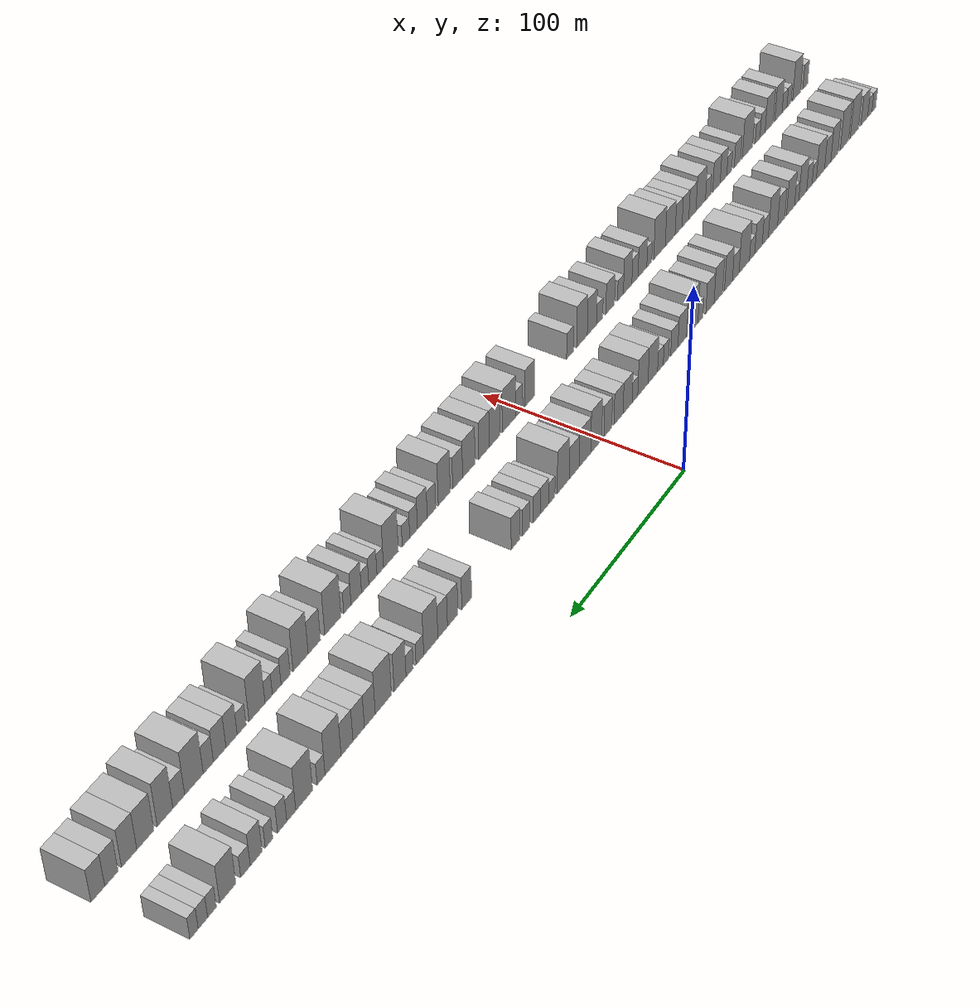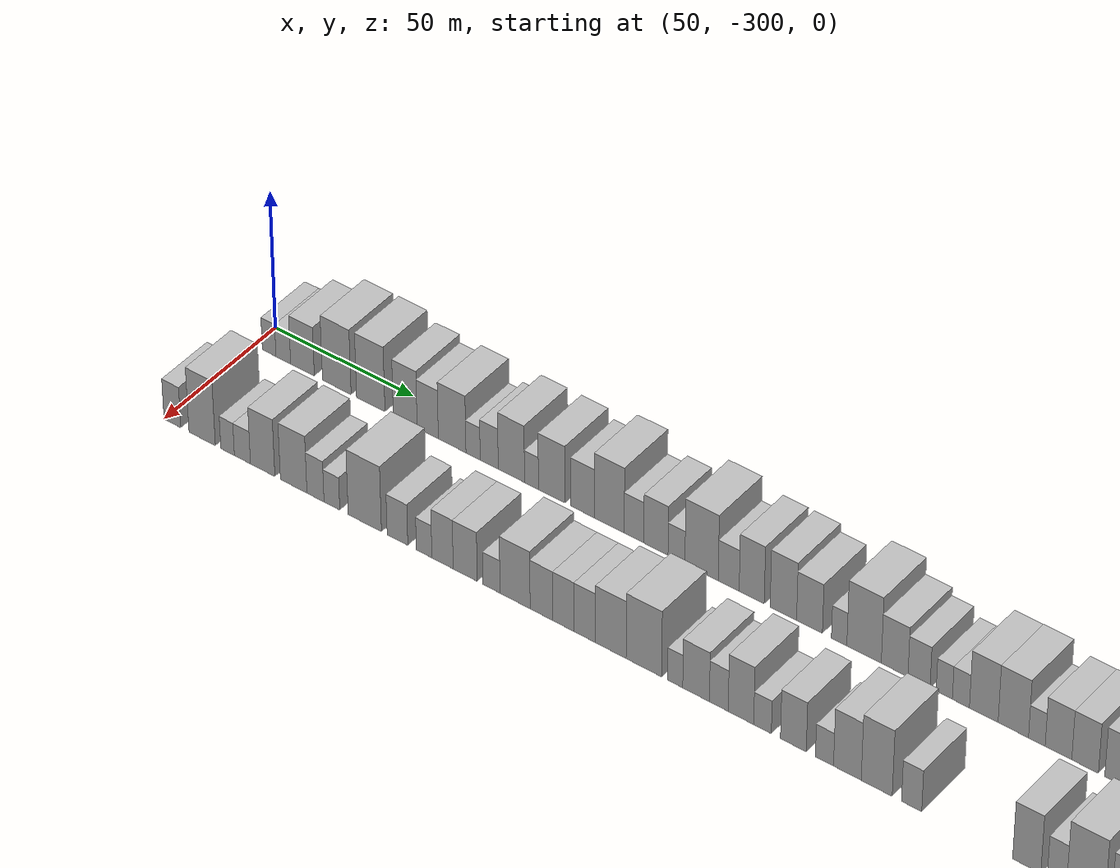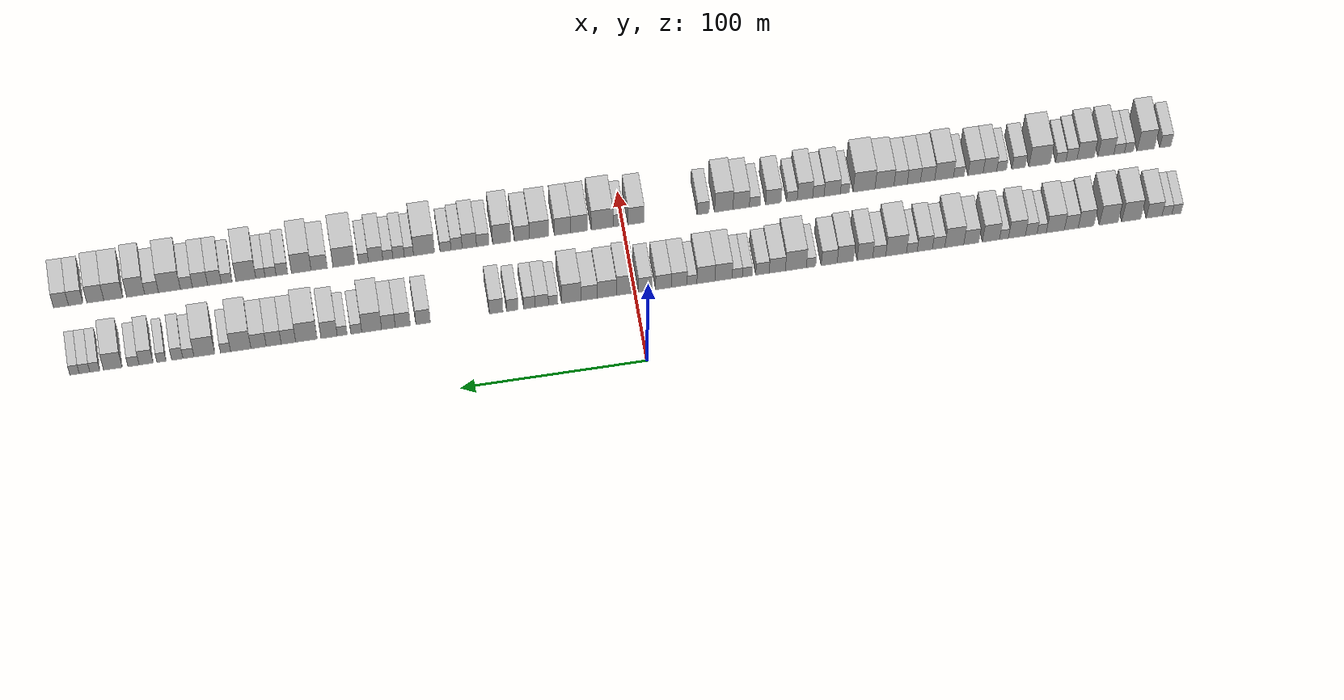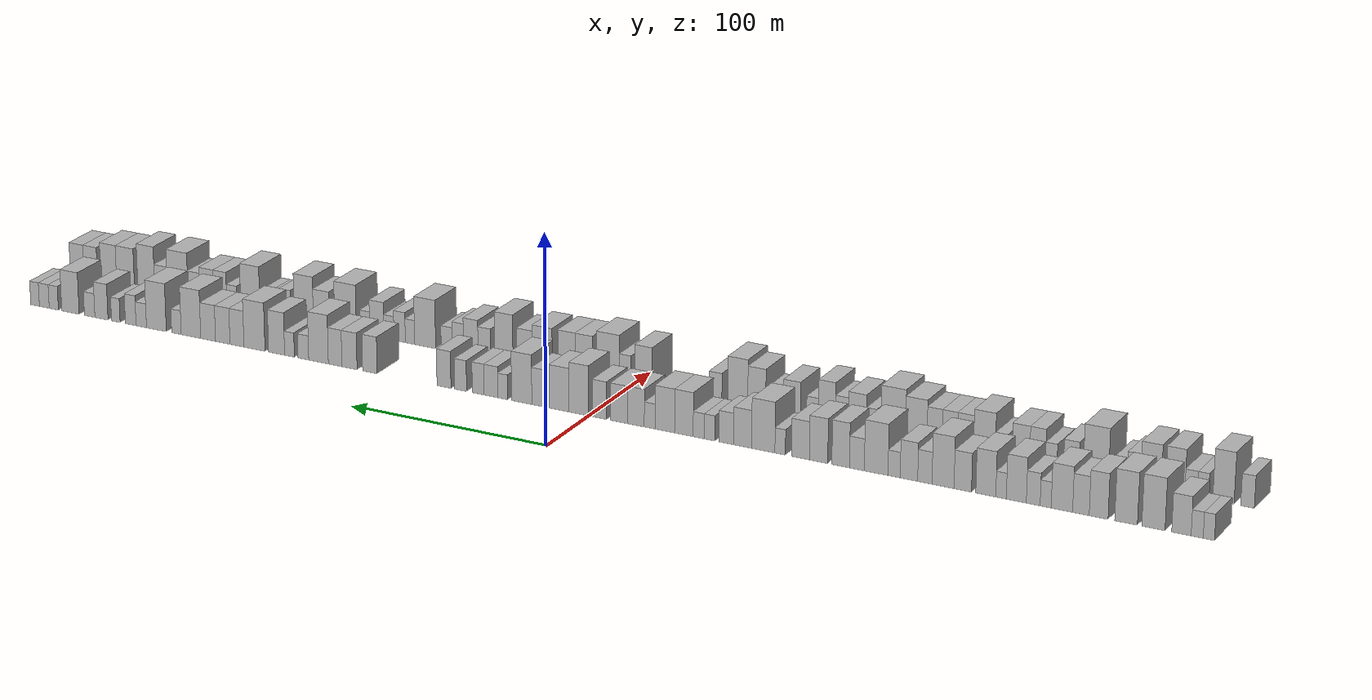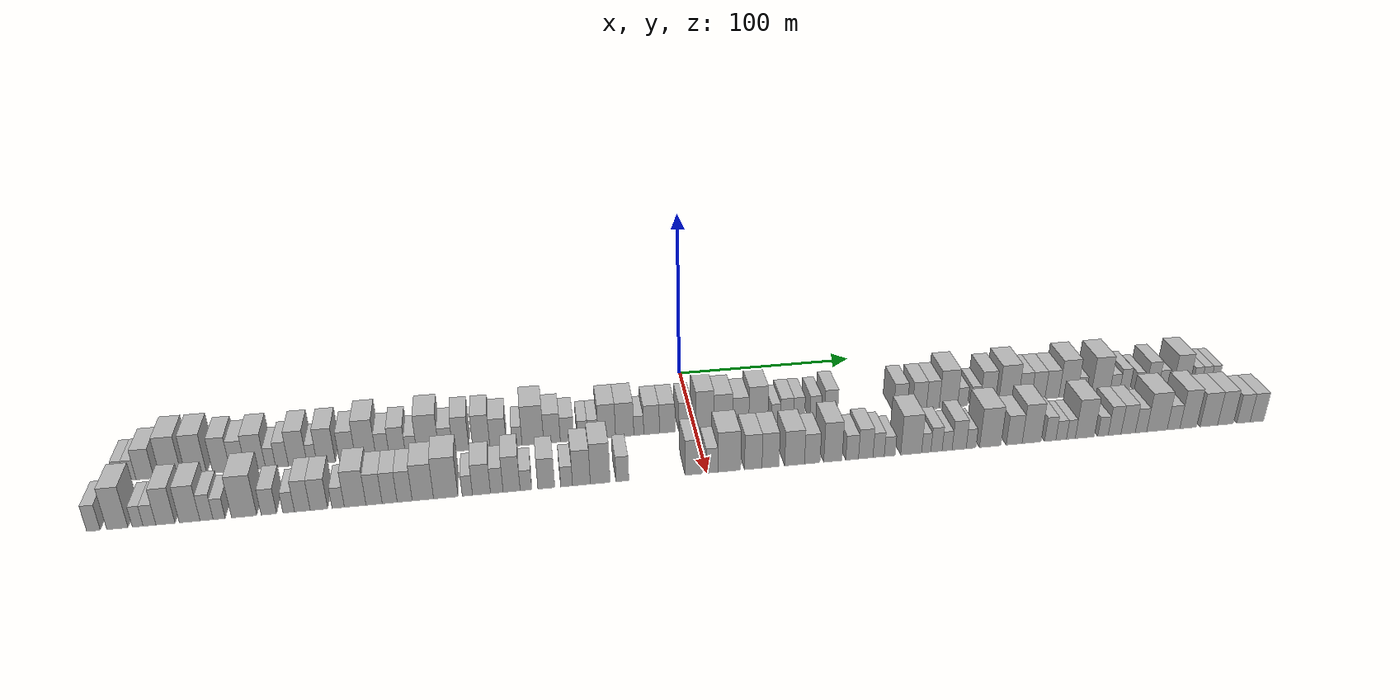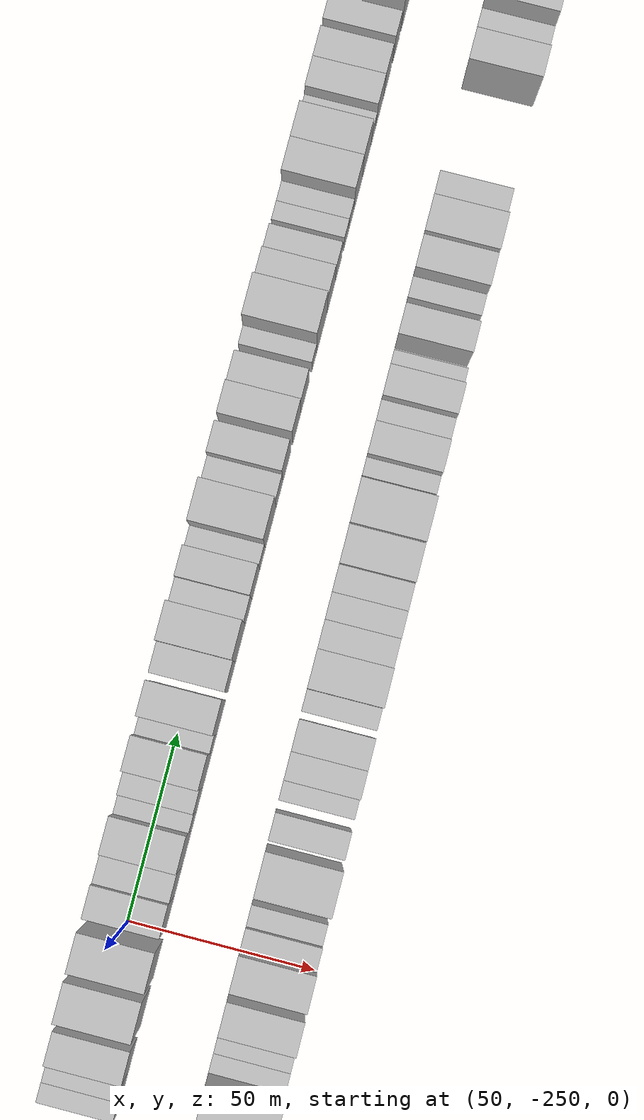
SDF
<sdf version="1.6">
 <world name="default">
  <scene>
   <sky><clouds><speed>12</speed></clouds></sky>
   <ambient>0.4 0.4 0.4 1</ambient>
   <background>0.7 0.7 0.7 1</background>
   <shadows>1</shadows>
  </scene>
  <gravity>0 0 -9.8066</gravity>
  <magnetic_field>6e-06 2.3e-05 -4.2e-05</magnetic_field>
  <physics default="0" name="default_physics" type="ode">
   <ode>
    <solver>
     <type>quick</type>
     <iters>10</iters>
     <sor>1.0</sor>
     <use_dynamic_moi_rescaling>0</use_dynamic_moi_rescaling>
    </solver>
    <constraints>
     <cfm>0</cfm>
     <erp>0.2</erp>
     <contact_max_correcting_vel>100</contact_max_correcting_vel>
     <contact_surface_layer>0.001</contact_surface_layer>
    </constraints>
   </ode>
   <max_step_size>0.004</max_step_size>
   <real_time_factor>1</real_time_factor>
   <real_time_update_rate>250</real_time_update_rate>
  </physics>
  <light name="sun" type="directional">
   <pose>0 0 10 0 0 0</pose>
   <diffuse>0.8 0.8 0.8 1</diffuse>
   <specular>0.2 0.2 0.2 1</specular>
   <attenuation>
    <range>1000</range>
    <constant>0.9</constant>
    <linear>0.01</linear>
    <quadratic>0.001</quadratic>
   </attenuation>
   <direction>-0.5 0.1 -0.9</direction>
  </light>
  <model name="building_1">
   <static>1</static>
   <pose>50.0000 -294.4814 0 0.000000 0.000000 0.000000</pose>
   <link name="link">
    <pose>0 0 6.00 0 0 0</pose>
    <collision name="collision"><geometry><box><size>20.0000 5.0373 12.0000</size></box></geometry></collision>
    <visual name="visual">
     <cast_shadows>0</cast_shadows>
     <geometry><box><size>20.0000 5.0373 12.0000</size></box></geometry>
     <material>
      <script>
       <uri>model://HANNAS_wall/materials/scripts</uri>
       <uri>model://HANNAS_wall/materials/textures</uri>
       <name>vrc/HANNAS_wall</name>
      </script>
     </material>
    </visual>
   </link>
  </model>
  <model name="building_2">
   <static>1</static>
   <pose>50.0000 -289.2743 0 0.000000 0.000000 0.000000</pose>
   <link name="link">
    <pose>0 0 6.00 0 0 0</pose>
    <collision name="collision"><geometry><box><size>20.0000 5.3769 12.0000</size></box></geometry></collision>
    <visual name="visual">
     <cast_shadows>0</cast_shadows>
     <geometry><box><size>20.0000 5.3769 12.0000</size></box></geometry>
     <material>
      <script>
       <uri>model://HANNAS_wall/materials/scripts</uri>
       <uri>model://HANNAS_wall/materials/textures</uri>
       <name>vrc/HANNAS_wall</name>
      </script>
     </material>
    </visual>
   </link>
  </model>
  <model name="building_3">
   <static>1</static>
   <pose>50.0000 -282.2469 0 0.000000 0.000000 0.000000</pose>
   <link name="link">
    <pose>0 0 9.00 0 0 0</pose>
    <collision name="collision"><geometry><box><size>20.0000 8.6779 18.0000</size></box></geometry></collision>
    <visual name="visual">
     <cast_shadows>0</cast_shadows>
     <geometry><box><size>20.0000 8.6779 18.0000</size></box></geometry>
     <material>
      <script>
       <uri>model://HANNAS_wall/materials/scripts</uri>
       <uri>model://HANNAS_wall/materials/textures</uri>
       <name>vrc/HANNAS_wall</name>
      </script>
     </material>
    </visual>
   </link>
  </model>
  <model name="building_4">
   <static>1</static>
   <pose>50.0000 -269.6992 0 0.000000 0.000000 0.000000</pose>
   <link name="link">
    <pose>0 0 12.00 0 0 0</pose>
    <collision name="collision"><geometry><box><size>20.0000 10.4175 24.0000</size></box></geometry></collision>
    <visual name="visual">
     <cast_shadows>0</cast_shadows>
     <geometry><box><size>20.0000 10.4175 24.0000</size></box></geometry>
     <material>
      <script>
       <uri>model://HANNAS_wall/materials/scripts</uri>
       <uri>model://HANNAS_wall/materials/textures</uri>
       <name>vrc/HANNAS_wall</name>
      </script>
     </material>
    </visual>
   </link>
  </model>
  <model name="building_5">
   <static>1</static>
   <pose>50.0000 -257.3596 0 0.000000 0.000000 0.000000</pose>
   <link name="link">
    <pose>0 0 12.00 0 0 0</pose>
    <collision name="collision"><geometry><box><size>20.0000 10.2619 24.0000</size></box></geometry></collision>
    <visual name="visual">
     <cast_shadows>0</cast_shadows>
     <geometry><box><size>20.0000 10.2619 24.0000</size></box></geometry>
     <material>
      <script>
       <uri>model://HANNAS_wall/materials/scripts</uri>
       <uri>model://HANNAS_wall/materials/textures</uri>
       <name>vrc/HANNAS_wall</name>
      </script>
     </material>
    </visual>
   </link>
  </model>
  <model name="building_6">
   <static>1</static>
   <pose>50.0000 -244.9306 0 0.000000 0.000000 0.000000</pose>
   <link name="link">
    <pose>0 0 10.50 0 0 0</pose>
    <collision name="collision"><geometry><box><size>20.0000 8.5960 21.0000</size></box></geometry></collision>
    <visual name="visual">
     <cast_shadows>0</cast_shadows>
     <geometry><box><size>20.0000 8.5960 21.0000</size></box></geometry>
     <material>
      <script>
       <uri>model://HANNAS_wall/materials/scripts</uri>
       <uri>model://HANNAS_wall/materials/textures</uri>
       <name>vrc/HANNAS_wall</name>
      </script>
     </material>
    </visual>
   </link>
  </model>
  <model name="building_7">
   <static>1</static>
   <pose>50.0000 -236.8442 0 0.000000 0.000000 0.000000</pose>
   <link name="link">
    <pose>0 0 9.00 0 0 0</pose>
    <collision name="collision"><geometry><box><size>20.0000 7.5769 18.0000</size></box></geometry></collision>
    <visual name="visual">
     <cast_shadows>0</cast_shadows>
     <geometry><box><size>20.0000 7.5769 18.0000</size></box></geometry>
     <material>
      <script>
       <uri>model://HANNAS_wall/materials/scripts</uri>
       <uri>model://HANNAS_wall/materials/textures</uri>
       <name>vrc/HANNAS_wall</name>
      </script>
     </material>
    </visual>
   </link>
  </model>
  <model name="building_8">
   <static>1</static>
   <pose>50.0000 -228.1408 0 0.000000 0.000000 0.000000</pose>
   <link name="link">
    <pose>0 0 10.50 0 0 0</pose>
    <collision name="collision"><geometry><box><size>20.0000 9.8300 21.0000</size></box></geometry></collision>
    <visual name="visual">
     <cast_shadows>0</cast_shadows>
     <geometry><box><size>20.0000 9.8300 21.0000</size></box></geometry>
     <material>
      <script>
       <uri>model://HANNAS_wall/materials/scripts</uri>
       <uri>model://HANNAS_wall/materials/textures</uri>
       <name>vrc/HANNAS_wall</name>
      </script>
     </material>
    </visual>
   </link>
  </model>
  <model name="building_9">
   <static>1</static>
   <pose>50.0000 -220.6946 0 0.000000 0.000000 0.000000</pose>
   <link name="link">
    <pose>0 0 6.00 0 0 0</pose>
    <collision name="collision"><geometry><box><size>20.0000 5.0625 12.0000</size></box></geometry></collision>
    <visual name="visual">
     <cast_shadows>0</cast_shadows>
     <geometry><box><size>20.0000 5.0625 12.0000</size></box></geometry>
     <material>
      <script>
       <uri>model://HANNAS_wall/materials/scripts</uri>
       <uri>model://HANNAS_wall/materials/textures</uri>
       <name>vrc/HANNAS_wall</name>
      </script>
     </material>
    </visual>
   </link>
  </model>
  <model name="building_10">
   <static>1</static>
   <pose>50.0000 -214.9720 0 0.000000 0.000000 0.000000</pose>
   <link name="link">
    <pose>0 0 7.50 0 0 0</pose>
    <collision name="collision"><geometry><box><size>20.0000 6.3826 15.0000</size></box></geometry></collision>
    <visual name="visual">
     <cast_shadows>0</cast_shadows>
     <geometry><box><size>20.0000 6.3826 15.0000</size></box></geometry>
     <material>
      <script>
       <uri>model://HANNAS_wall/materials/scripts</uri>
       <uri>model://HANNAS_wall/materials/textures</uri>
       <name>vrc/HANNAS_wall</name>
      </script>
     </material>
    </visual>
   </link>
  </model>
  <model name="building_11">
   <static>1</static>
   <pose>50.0000 -207.1445 0 0.000000 0.000000 0.000000</pose>
   <link name="link">
    <pose>0 0 10.50 0 0 0</pose>
    <collision name="collision"><geometry><box><size>20.0000 9.2723 21.0000</size></box></geometry></collision>
    <visual name="visual">
     <cast_shadows>0</cast_shadows>
     <geometry><box><size>20.0000 9.2723 21.0000</size></box></geometry>
     <material>
      <script>
       <uri>model://HANNAS_wall/materials/scripts</uri>
       <uri>model://HANNAS_wall/materials/textures</uri>
       <name>vrc/HANNAS_wall</name>
      </script>
     </material>
    </visual>
   </link>
  </model>
  <model name="building_12">
   <static>1</static>
   <pose>50.0000 -200.0656 0 0.000000 0.000000 0.000000</pose>
   <link name="link">
    <pose>0 0 6.00 0 0 0</pose>
    <collision name="collision"><geometry><box><size>20.0000 4.8856 12.0000</size></box></geometry></collision>
    <visual name="visual">
     <cast_shadows>0</cast_shadows>
     <geometry><box><size>20.0000 4.8856 12.0000</size></box></geometry>
     <material>
      <script>
       <uri>model://HANNAS_wall/materials/scripts</uri>
       <uri>model://HANNAS_wall/materials/textures</uri>
       <name>vrc/HANNAS_wall</name>
      </script>
     </material>
    </visual>
   </link>
  </model>
  <model name="building_13">
   <static>1</static>
   <pose>50.0000 -192.9678 0 0.000000 0.000000 0.000000</pose>
   <link name="link">
    <pose>0 0 10.50 0 0 0</pose>
    <collision name="collision"><geometry><box><size>20.0000 9.3100 21.0000</size></box></geometry></collision>
    <visual name="visual">
     <cast_shadows>0</cast_shadows>
     <geometry><box><size>20.0000 9.3100 21.0000</size></box></geometry>
     <material>
      <script>
       <uri>model://HANNAS_wall/materials/scripts</uri>
       <uri>model://HANNAS_wall/materials/textures</uri>
       <name>vrc/HANNAS_wall</name>
      </script>
     </material>
    </visual>
   </link>
  </model>
  <model name="building_14">
   <static>1</static>
   <pose>50.0000 -182.2153 0 0.000000 0.000000 0.000000</pose>
   <link name="link">
    <pose>0 0 9.00 0 0 0</pose>
    <collision name="collision"><geometry><box><size>20.0000 8.1949 18.0000</size></box></geometry></collision>
    <visual name="visual">
     <cast_shadows>0</cast_shadows>
     <geometry><box><size>20.0000 8.1949 18.0000</size></box></geometry>
     <material>
      <script>
       <uri>model://HANNAS_wall/materials/scripts</uri>
       <uri>model://HANNAS_wall/materials/textures</uri>
       <name>vrc/HANNAS_wall</name>
      </script>
     </material>
    </visual>
   </link>
  </model>
  <model name="building_15">
   <static>1</static>
   <pose>50.0000 -172.9326 0 0.000000 0.000000 0.000000</pose>
   <link name="link">
    <pose>0 0 12.00 0 0 0</pose>
    <collision name="collision"><geometry><box><size>20.0000 10.3706 24.0000</size></box></geometry></collision>
    <visual name="visual">
     <cast_shadows>0</cast_shadows>
     <geometry><box><size>20.0000 10.3706 24.0000</size></box></geometry>
     <material>
      <script>
       <uri>model://HANNAS_wall/materials/scripts</uri>
       <uri>model://HANNAS_wall/materials/textures</uri>
       <name>vrc/HANNAS_wall</name>
      </script>
     </material>
    </visual>
   </link>
  </model>
  <model name="building_16">
   <static>1</static>
   <pose>50.0000 -164.3762 0 0.000000 0.000000 0.000000</pose>
   <link name="link">
    <pose>0 0 7.50 0 0 0</pose>
    <collision name="collision"><geometry><box><size>20.0000 6.7421 15.0000</size></box></geometry></collision>
    <visual name="visual">
     <cast_shadows>0</cast_shadows>
     <geometry><box><size>20.0000 6.7421 15.0000</size></box></geometry>
     <material>
      <script>
       <uri>model://HANNAS_wall/materials/scripts</uri>
       <uri>model://HANNAS_wall/materials/textures</uri>
       <name>vrc/HANNAS_wall</name>
      </script>
     </material>
    </visual>
   </link>
  </model>
  <model name="building_17">
   <static>1</static>
   <pose>50.0000 -156.8604 0 0.000000 0.000000 0.000000</pose>
   <link name="link">
    <pose>0 0 9.00 0 0 0</pose>
    <collision name="collision"><geometry><box><size>20.0000 8.2895 18.0000</size></box></geometry></collision>
    <visual name="visual">
     <cast_shadows>0</cast_shadows>
     <geometry><box><size>20.0000 8.2895 18.0000</size></box></geometry>
     <material>
      <script>
       <uri>model://HANNAS_wall/materials/scripts</uri>
       <uri>model://HANNAS_wall/materials/textures</uri>
       <name>vrc/HANNAS_wall</name>
      </script>
     </material>
    </visual>
   </link>
  </model>
  <model name="building_18">
   <static>1</static>
   <pose>50.0000 -149.8223 0 0.000000 0.000000 0.000000</pose>
   <link name="link">
    <pose>0 0 6.00 0 0 0</pose>
    <collision name="collision"><geometry><box><size>20.0000 5.7867 12.0000</size></box></geometry></collision>
    <visual name="visual">
     <cast_shadows>0</cast_shadows>
     <geometry><box><size>20.0000 5.7867 12.0000</size></box></geometry>
     <material>
      <script>
       <uri>model://HANNAS_wall/materials/scripts</uri>
       <uri>model://HANNAS_wall/materials/textures</uri>
       <name>vrc/HANNAS_wall</name>
      </script>
     </material>
    </visual>
   </link>
  </model>
  <model name="building_19">
   <static>1</static>
   <pose>50.0000 -141.2741 0 0.000000 0.000000 0.000000</pose>
   <link name="link">
    <pose>0 0 12.00 0 0 0</pose>
    <collision name="collision"><geometry><box><size>20.0000 11.3098 24.0000</size></box></geometry></collision>
    <visual name="visual">
     <cast_shadows>0</cast_shadows>
     <geometry><box><size>20.0000 11.3098 24.0000</size></box></geometry>
     <material>
      <script>
       <uri>model://HANNAS_wall/materials/scripts</uri>
       <uri>model://HANNAS_wall/materials/textures</uri>
       <name>vrc/HANNAS_wall</name>
      </script>
     </material>
    </visual>
   </link>
  </model>
  <model name="building_20">
   <static>1</static>
   <pose>50.0000 -132.0643 0 0.000000 0.000000 0.000000</pose>
   <link name="link">
    <pose>0 0 7.50 0 0 0</pose>
    <collision name="collision"><geometry><box><size>20.0000 7.1097 15.0000</size></box></geometry></collision>
    <visual name="visual">
     <cast_shadows>0</cast_shadows>
     <geometry><box><size>20.0000 7.1097 15.0000</size></box></geometry>
     <material>
      <script>
       <uri>model://HANNAS_wall/materials/scripts</uri>
       <uri>model://HANNAS_wall/materials/textures</uri>
       <name>vrc/HANNAS_wall</name>
      </script>
     </material>
    </visual>
   </link>
  </model>
  <model name="building_21">
   <static>1</static>
   <pose>50.0000 -124.2901 0 0.000000 0.000000 0.000000</pose>
   <link name="link">
    <pose>0 0 10.50 0 0 0</pose>
    <collision name="collision"><geometry><box><size>20.0000 8.4387 21.0000</size></box></geometry></collision>
    <visual name="visual">
     <cast_shadows>0</cast_shadows>
     <geometry><box><size>20.0000 8.4387 21.0000</size></box></geometry>
     <material>
      <script>
       <uri>model://HANNAS_wall/materials/scripts</uri>
       <uri>model://HANNAS_wall/materials/textures</uri>
       <name>vrc/HANNAS_wall</name>
      </script>
     </material>
    </visual>
   </link>
  </model>
  <model name="building_22">
   <static>1</static>
   <pose>50.0000 -113.6414 0 0.000000 0.000000 0.000000</pose>
   <link name="link">
    <pose>0 0 10.50 0 0 0</pose>
    <collision name="collision"><geometry><box><size>20.0000 8.8589 21.0000</size></box></geometry></collision>
    <visual name="visual">
     <cast_shadows>0</cast_shadows>
     <geometry><box><size>20.0000 8.8589 21.0000</size></box></geometry>
     <material>
      <script>
       <uri>model://HANNAS_wall/materials/scripts</uri>
       <uri>model://HANNAS_wall/materials/textures</uri>
       <name>vrc/HANNAS_wall</name>
      </script>
     </material>
    </visual>
   </link>
  </model>
  <model name="building_23">
   <static>1</static>
   <pose>50.0000 -104.8949 0 0.000000 0.000000 0.000000</pose>
   <link name="link">
    <pose>0 0 9.00 0 0 0</pose>
    <collision name="collision"><geometry><box><size>20.0000 8.6341 18.0000</size></box></geometry></collision>
    <visual name="visual">
     <cast_shadows>0</cast_shadows>
     <geometry><box><size>20.0000 8.6341 18.0000</size></box></geometry>
     <material>
      <script>
       <uri>model://HANNAS_wall/materials/scripts</uri>
       <uri>model://HANNAS_wall/materials/textures</uri>
       <name>vrc/HANNAS_wall</name>
      </script>
     </material>
    </visual>
   </link>
  </model>
  <model name="building_24">
   <static>1</static>
   <pose>50.0000 -95.0213 0 0.000000 0.000000 0.000000</pose>
   <link name="link">
    <pose>0 0 6.00 0 0 0</pose>
    <collision name="collision"><geometry><box><size>20.0000 5.1131 12.0000</size></box></geometry></collision>
    <visual name="visual">
     <cast_shadows>0</cast_shadows>
     <geometry><box><size>20.0000 5.1131 12.0000</size></box></geometry>
     <material>
      <script>
       <uri>model://HANNAS_wall/materials/scripts</uri>
       <uri>model://HANNAS_wall/materials/textures</uri>
       <name>vrc/HANNAS_wall</name>
      </script>
     </material>
    </visual>
   </link>
  </model>
  <model name="building_25">
   <static>1</static>
   <pose>50.0000 -86.7722 0 0.000000 0.000000 0.000000</pose>
   <link name="link">
    <pose>0 0 12.00 0 0 0</pose>
    <collision name="collision"><geometry><box><size>20.0000 11.3852 24.0000</size></box></geometry></collision>
    <visual name="visual">
     <cast_shadows>0</cast_shadows>
     <geometry><box><size>20.0000 11.3852 24.0000</size></box></geometry>
     <material>
      <script>
       <uri>model://HANNAS_wall/materials/scripts</uri>
       <uri>model://HANNAS_wall/materials/textures</uri>
       <name>vrc/HANNAS_wall</name>
      </script>
     </material>
    </visual>
   </link>
  </model>
  <model name="building_26">
   <static>1</static>
   <pose>50.0000 -76.6967 0 0.000000 0.000000 0.000000</pose>
   <link name="link">
    <pose>0 0 9.00 0 0 0</pose>
    <collision name="collision"><geometry><box><size>20.0000 8.7659 18.0000</size></box></geometry></collision>
    <visual name="visual">
     <cast_shadows>0</cast_shadows>
     <geometry><box><size>20.0000 8.7659 18.0000</size></box></geometry>
     <material>
      <script>
       <uri>model://HANNAS_wall/materials/scripts</uri>
       <uri>model://HANNAS_wall/materials/textures</uri>
       <name>vrc/HANNAS_wall</name>
      </script>
     </material>
    </visual>
   </link>
  </model>
  <model name="building_27">
   <static>1</static>
   <pose>50.0000 -68.6961 0 0.000000 0.000000 0.000000</pose>
   <link name="link">
    <pose>0 0 7.50 0 0 0</pose>
    <collision name="collision"><geometry><box><size>20.0000 7.2352 15.0000</size></box></geometry></collision>
    <visual name="visual">
     <cast_shadows>0</cast_shadows>
     <geometry><box><size>20.0000 7.2352 15.0000</size></box></geometry>
     <material>
      <script>
       <uri>model://HANNAS_wall/materials/scripts</uri>
       <uri>model://HANNAS_wall/materials/textures</uri>
       <name>vrc/HANNAS_wall</name>
      </script>
     </material>
    </visual>
   </link>
  </model>
  <model name="building_28">
   <static>1</static>
   <pose>50.0000 -60.4429 0 0.000000 0.000000 0.000000</pose>
   <link name="link">
    <pose>0 0 6.00 0 0 0</pose>
    <collision name="collision"><geometry><box><size>20.0000 5.2712 12.0000</size></box></geometry></collision>
    <visual name="visual">
     <cast_shadows>0</cast_shadows>
     <geometry><box><size>20.0000 5.2712 12.0000</size></box></geometry>
     <material>
      <script>
       <uri>model://HANNAS_wall/materials/scripts</uri>
       <uri>model://HANNAS_wall/materials/textures</uri>
       <name>vrc/HANNAS_wall</name>
      </script>
     </material>
    </visual>
   </link>
  </model>
  <model name="building_29">
   <static>1</static>
   <pose>50.0000 -55.0356 0 0.000000 0.000000 0.000000</pose>
   <link name="link">
    <pose>0 0 6.00 0 0 0</pose>
    <collision name="collision"><geometry><box><size>20.0000 5.5434 12.0000</size></box></geometry></collision>
    <visual name="visual">
     <cast_shadows>0</cast_shadows>
     <geometry><box><size>20.0000 5.5434 12.0000</size></box></geometry>
     <material>
      <script>
       <uri>model://HANNAS_wall/materials/scripts</uri>
       <uri>model://HANNAS_wall/materials/textures</uri>
       <name>vrc/HANNAS_wall</name>
      </script>
     </material>
    </visual>
   </link>
  </model>
  <model name="building_30">
   <static>1</static>
   <pose>50.0000 -47.6244 0 0.000000 0.000000 0.000000</pose>
   <link name="link">
    <pose>0 0 10.50 0 0 0</pose>
    <collision name="collision"><geometry><box><size>20.0000 9.2790 21.0000</size></box></geometry></collision>
    <visual name="visual">
     <cast_shadows>0</cast_shadows>
     <geometry><box><size>20.0000 9.2790 21.0000</size></box></geometry>
     <material>
      <script>
       <uri>model://HANNAS_wall/materials/scripts</uri>
       <uri>model://HANNAS_wall/materials/textures</uri>
       <name>vrc/HANNAS_wall</name>
      </script>
     </material>
    </visual>
   </link>
  </model>
  <model name="building_31">
   <static>1</static>
   <pose>50.0000 -38.0883 0 0.000000 0.000000 0.000000</pose>
   <link name="link">
    <pose>0 0 10.50 0 0 0</pose>
    <collision name="collision"><geometry><box><size>20.0000 9.7932 21.0000</size></box></geometry></collision>
    <visual name="visual">
     <cast_shadows>0</cast_shadows>
     <geometry><box><size>20.0000 9.7932 21.0000</size></box></geometry>
     <material>
      <script>
       <uri>model://HANNAS_wall/materials/scripts</uri>
       <uri>model://HANNAS_wall/materials/textures</uri>
       <name>vrc/HANNAS_wall</name>
      </script>
     </material>
    </visual>
   </link>
  </model>
  <model name="building_32">
   <static>1</static>
   <pose>50.0000 -30.5219 0 0.000000 0.000000 0.000000</pose>
   <link name="link">
    <pose>0 0 6.00 0 0 0</pose>
    <collision name="collision"><geometry><box><size>20.0000 5.3396 12.0000</size></box></geometry></collision>
    <visual name="visual">
     <cast_shadows>0</cast_shadows>
     <geometry><box><size>20.0000 5.3396 12.0000</size></box></geometry>
     <material>
      <script>
       <uri>model://HANNAS_wall/materials/scripts</uri>
       <uri>model://HANNAS_wall/materials/textures</uri>
       <name>vrc/HANNAS_wall</name>
      </script>
     </material>
    </visual>
   </link>
  </model>
  <model name="building_33">
   <static>1</static>
   <pose>50.0000 -23.6054 0 0.000000 0.000000 0.000000</pose>
   <link name="link">
    <pose>0 0 9.00 0 0 0</pose>
    <collision name="collision"><geometry><box><size>20.0000 8.4933 18.0000</size></box></geometry></collision>
    <visual name="visual">
     <cast_shadows>0</cast_shadows>
     <geometry><box><size>20.0000 8.4933 18.0000</size></box></geometry>
     <material>
      <script>
       <uri>model://HANNAS_wall/materials/scripts</uri>
       <uri>model://HANNAS_wall/materials/textures</uri>
       <name>vrc/HANNAS_wall</name>
      </script>
     </material>
    </visual>
   </link>
  </model>
  <model name="building_34">
   <static>1</static>
   <pose>50.0000 -15.1168 0 0.000000 0.000000 0.000000</pose>
   <link name="link">
    <pose>0 0 9.00 0 0 0</pose>
    <collision name="collision"><geometry><box><size>20.0000 8.4840 18.0000</size></box></geometry></collision>
    <visual name="visual">
     <cast_shadows>0</cast_shadows>
     <geometry><box><size>20.0000 8.4840 18.0000</size></box></geometry>
     <material>
      <script>
       <uri>model://HANNAS_wall/materials/scripts</uri>
       <uri>model://HANNAS_wall/materials/textures</uri>
       <name>vrc/HANNAS_wall</name>
      </script>
     </material>
    </visual>
   </link>
  </model>
  <model name="building_35">
   <static>1</static>
   <pose>50.0000 -5.2553 0 0.000000 0.000000 0.000000</pose>
   <link name="link">
    <pose>0 0 9.00 0 0 0</pose>
    <collision name="collision"><geometry><box><size>20.0000 7.2390 18.0000</size></box></geometry></collision>
    <visual name="visual">
     <cast_shadows>0</cast_shadows>
     <geometry><box><size>20.0000 7.2390 18.0000</size></box></geometry>
     <material>
      <script>
       <uri>model://HANNAS_wall/materials/scripts</uri>
       <uri>model://HANNAS_wall/materials/textures</uri>
       <name>vrc/HANNAS_wall</name>
      </script>
     </material>
    </visual>
   </link>
  </model>
  <model name="building_36">
   <static>1</static>
   <pose>50.0000 5.2989 0 0.000000 0.000000 0.000000</pose>
   <link name="link">
    <pose>0 0 12.00 0 0 0</pose>
    <collision name="collision"><geometry><box><size>20.0000 9.8693 24.0000</size></box></geometry></collision>
    <visual name="visual">
     <cast_shadows>0</cast_shadows>
     <geometry><box><size>20.0000 9.8693 24.0000</size></box></geometry>
     <material>
      <script>
       <uri>model://HANNAS_wall/materials/scripts</uri>
       <uri>model://HANNAS_wall/materials/textures</uri>
       <name>vrc/HANNAS_wall</name>
      </script>
     </material>
    </visual>
   </link>
  </model>
  <model name="building_37">
   <static>1</static>
   <pose>50.0000 15.3436 0 0.000000 0.000000 0.000000</pose>
   <link name="link">
    <pose>0 0 10.50 0 0 0</pose>
    <collision name="collision"><geometry><box><size>20.0000 10.2202 21.0000</size></box></geometry></collision>
    <visual name="visual">
     <cast_shadows>0</cast_shadows>
     <geometry><box><size>20.0000 10.2202 21.0000</size></box></geometry>
     <material>
      <script>
       <uri>model://HANNAS_wall/materials/scripts</uri>
       <uri>model://HANNAS_wall/materials/textures</uri>
       <name>vrc/HANNAS_wall</name>
      </script>
     </material>
    </visual>
   </link>
  </model>
  <model name="building_38">
   <static>1</static>
   <pose>50.0000 24.9056 0 0.000000 0.000000 0.000000</pose>
   <link name="link">
    <pose>0 0 9.00 0 0 0</pose>
    <collision name="collision"><geometry><box><size>20.0000 8.9036 18.0000</size></box></geometry></collision>
    <visual name="visual">
     <cast_shadows>0</cast_shadows>
     <geometry><box><size>20.0000 8.9036 18.0000</size></box></geometry>
     <material>
      <script>
       <uri>model://HANNAS_wall/materials/scripts</uri>
       <uri>model://HANNAS_wall/materials/textures</uri>
       <name>vrc/HANNAS_wall</name>
      </script>
     </material>
    </visual>
   </link>
  </model>
  <model name="building_39">
   <static>1</static>
   <pose>50.0000 34.5835 0 0.000000 0.000000 0.000000</pose>
   <link name="link">
    <pose>0 0 12.00 0 0 0</pose>
    <collision name="collision"><geometry><box><size>20.0000 10.4523 24.0000</size></box></geometry></collision>
    <visual name="visual">
     <cast_shadows>0</cast_shadows>
     <geometry><box><size>20.0000 10.4523 24.0000</size></box></geometry>
     <material>
      <script>
       <uri>model://HANNAS_wall/materials/scripts</uri>
       <uri>model://HANNAS_wall/materials/textures</uri>
       <name>vrc/HANNAS_wall</name>
      </script>
     </material>
    </visual>
   </link>
  </model>
  <model name="building_40">
   <static>1</static>
   <pose>50.0000 44.3643 0 0.000000 0.000000 0.000000</pose>
   <link name="link">
    <pose>0 0 6.00 0 0 0</pose>
    <collision name="collision"><geometry><box><size>20.0000 5.1094 12.0000</size></box></geometry></collision>
    <visual name="visual">
     <cast_shadows>0</cast_shadows>
     <geometry><box><size>20.0000 5.1094 12.0000</size></box></geometry>
     <material>
      <script>
       <uri>model://HANNAS_wall/materials/scripts</uri>
       <uri>model://HANNAS_wall/materials/textures</uri>
       <name>vrc/HANNAS_wall</name>
      </script>
     </material>
    </visual>
   </link>
  </model>
  <model name="building_41">
   <static>1</static>
   <pose>50.0000 50.5406 0 0.000000 0.000000 0.000000</pose>
   <link name="link">
    <pose>0 0 7.50 0 0 0</pose>
    <collision name="collision"><geometry><box><size>20.0000 7.2432 15.0000</size></box></geometry></collision>
    <visual name="visual">
     <cast_shadows>0</cast_shadows>
     <geometry><box><size>20.0000 7.2432 15.0000</size></box></geometry>
     <material>
      <script>
       <uri>model://HANNAS_wall/materials/scripts</uri>
       <uri>model://HANNAS_wall/materials/textures</uri>
       <name>vrc/HANNAS_wall</name>
      </script>
     </material>
    </visual>
   </link>
  </model>
  <model name="building_42">
   <static>1</static>
   <pose>50.0000 57.1868 0 0.000000 0.000000 0.000000</pose>
   <link name="link">
    <pose>0 0 7.50 0 0 0</pose>
    <collision name="collision"><geometry><box><size>20.0000 6.0493 15.0000</size></box></geometry></collision>
    <visual name="visual">
     <cast_shadows>0</cast_shadows>
     <geometry><box><size>20.0000 6.0493 15.0000</size></box></geometry>
     <material>
      <script>
       <uri>model://HANNAS_wall/materials/scripts</uri>
       <uri>model://HANNAS_wall/materials/textures</uri>
       <name>vrc/HANNAS_wall</name>
      </script>
     </material>
    </visual>
   </link>
  </model>
  <model name="building_43">
   <static>1</static>
   <pose>50.0000 66.2984 0 0.000000 0.000000 0.000000</pose>
   <link name="link">
    <pose>0 0 7.50 0 0 0</pose>
    <collision name="collision"><geometry><box><size>20.0000 6.1739 15.0000</size></box></geometry></collision>
    <visual name="visual">
     <cast_shadows>0</cast_shadows>
     <geometry><box><size>20.0000 6.1739 15.0000</size></box></geometry>
     <material>
      <script>
       <uri>model://HANNAS_wall/materials/scripts</uri>
       <uri>model://HANNAS_wall/materials/textures</uri>
       <name>vrc/HANNAS_wall</name>
      </script>
     </material>
    </visual>
   </link>
  </model>
  <model name="building_44">
   <static>1</static>
   <pose>50.0000 75.0308 0 0.000000 0.000000 0.000000</pose>
   <link name="link">
    <pose>0 0 9.00 0 0 0</pose>
    <collision name="collision"><geometry><box><size>20.0000 7.2908 18.0000</size></box></geometry></collision>
    <visual name="visual">
     <cast_shadows>0</cast_shadows>
     <geometry><box><size>20.0000 7.2908 18.0000</size></box></geometry>
     <material>
      <script>
       <uri>model://HANNAS_wall/materials/scripts</uri>
       <uri>model://HANNAS_wall/materials/textures</uri>
       <name>vrc/HANNAS_wall</name>
      </script>
     </material>
    </visual>
   </link>
  </model>
  <model name="building_45">
   <static>1</static>
   <pose>50.0000 114.2790 0 0.000000 0.000000 0.000000</pose>
   <link name="link">
    <pose>0 0 9.00 0 0 0</pose>
    <collision name="collision"><geometry><box><size>20.0000 7.7352 18.0000</size></box></geometry></collision>
    <visual name="visual">
     <cast_shadows>0</cast_shadows>
     <geometry><box><size>20.0000 7.7352 18.0000</size></box></geometry>
     <material>
      <script>
       <uri>model://HANNAS_wall/materials/scripts</uri>
       <uri>model://HANNAS_wall/materials/textures</uri>
       <name>vrc/HANNAS_wall</name>
      </script>
     </material>
    </visual>
   </link>
  </model>
  <model name="building_46">
   <static>1</static>
   <pose>50.0000 125.1960 0 0.000000 0.000000 0.000000</pose>
   <link name="link">
    <pose>0 0 9.00 0 0 0</pose>
    <collision name="collision"><geometry><box><size>20.0000 8.0990 18.0000</size></box></geometry></collision>
    <visual name="visual">
     <cast_shadows>0</cast_shadows>
     <geometry><box><size>20.0000 8.0990 18.0000</size></box></geometry>
     <material>
      <script>
       <uri>model://HANNAS_wall/materials/scripts</uri>
       <uri>model://HANNAS_wall/materials/textures</uri>
       <name>vrc/HANNAS_wall</name>
      </script>
     </material>
    </visual>
   </link>
  </model>
  <model name="building_47">
   <static>1</static>
   <pose>50.0000 132.9051 0 0.000000 0.000000 0.000000</pose>
   <link name="link">
    <pose>0 0 9.00 0 0 0</pose>
    <collision name="collision"><geometry><box><size>20.0000 7.3190 18.0000</size></box></geometry></collision>
    <visual name="visual">
     <cast_shadows>0</cast_shadows>
     <geometry><box><size>20.0000 7.3190 18.0000</size></box></geometry>
     <material>
      <script>
       <uri>model://HANNAS_wall/materials/scripts</uri>
       <uri>model://HANNAS_wall/materials/textures</uri>
       <name>vrc/HANNAS_wall</name>
      </script>
     </material>
    </visual>
   </link>
  </model>
  <model name="building_48">
   <static>1</static>
   <pose>50.0000 141.8747 0 0.000000 0.000000 0.000000</pose>
   <link name="link">
    <pose>0 0 12.00 0 0 0</pose>
    <collision name="collision"><geometry><box><size>20.0000 10.6203 24.0000</size></box></geometry></collision>
    <visual name="visual">
     <cast_shadows>0</cast_shadows>
     <geometry><box><size>20.0000 10.6203 24.0000</size></box></geometry>
     <material>
      <script>
       <uri>model://HANNAS_wall/materials/scripts</uri>
       <uri>model://HANNAS_wall/materials/textures</uri>
       <name>vrc/HANNAS_wall</name>
      </script>
     </material>
    </visual>
   </link>
  </model>
  <model name="building_49">
   <static>1</static>
   <pose>50.0000 150.0842 0 0.000000 0.000000 0.000000</pose>
   <link name="link">
    <pose>0 0 6.00 0 0 0</pose>
    <collision name="collision"><geometry><box><size>20.0000 5.7988 12.0000</size></box></geometry></collision>
    <visual name="visual">
     <cast_shadows>0</cast_shadows>
     <geometry><box><size>20.0000 5.7988 12.0000</size></box></geometry>
     <material>
      <script>
       <uri>model://HANNAS_wall/materials/scripts</uri>
       <uri>model://HANNAS_wall/materials/textures</uri>
       <name>vrc/HANNAS_wall</name>
      </script>
     </material>
    </visual>
   </link>
  </model>
  <model name="building_50">
   <static>1</static>
   <pose>50.0000 157.6282 0 0.000000 0.000000 0.000000</pose>
   <link name="link">
    <pose>0 0 6.00 0 0 0</pose>
    <collision name="collision"><geometry><box><size>20.0000 5.2891 12.0000</size></box></geometry></collision>
    <visual name="visual">
     <cast_shadows>0</cast_shadows>
     <geometry><box><size>20.0000 5.2891 12.0000</size></box></geometry>
     <material>
      <script>
       <uri>model://HANNAS_wall/materials/scripts</uri>
       <uri>model://HANNAS_wall/materials/textures</uri>
       <name>vrc/HANNAS_wall</name>
      </script>
     </material>
    </visual>
   </link>
  </model>
  <model name="building_51">
   <static>1</static>
   <pose>50.0000 164.6378 0 0.000000 0.000000 0.000000</pose>
   <link name="link">
    <pose>0 0 10.50 0 0 0</pose>
    <collision name="collision"><geometry><box><size>20.0000 8.7301 21.0000</size></box></geometry></collision>
    <visual name="visual">
     <cast_shadows>0</cast_shadows>
     <geometry><box><size>20.0000 8.7301 21.0000</size></box></geometry>
     <material>
      <script>
       <uri>model://HANNAS_wall/materials/scripts</uri>
       <uri>model://HANNAS_wall/materials/textures</uri>
       <name>vrc/HANNAS_wall</name>
      </script>
     </material>
    </visual>
   </link>
  </model>
  <model name="building_52">
   <static>1</static>
   <pose>50.0000 176.7647 0 0.000000 0.000000 0.000000</pose>
   <link name="link">
    <pose>0 0 12.00 0 0 0</pose>
    <collision name="collision"><geometry><box><size>20.0000 11.5238 24.0000</size></box></geometry></collision>
    <visual name="visual">
     <cast_shadows>0</cast_shadows>
     <geometry><box><size>20.0000 11.5238 24.0000</size></box></geometry>
     <material>
      <script>
       <uri>model://HANNAS_wall/materials/scripts</uri>
       <uri>model://HANNAS_wall/materials/textures</uri>
       <name>vrc/HANNAS_wall</name>
      </script>
     </material>
    </visual>
   </link>
  </model>
  <model name="building_53">
   <static>1</static>
   <pose>50.0000 186.3840 0 0.000000 0.000000 0.000000</pose>
   <link name="link">
    <pose>0 0 9.00 0 0 0</pose>
    <collision name="collision"><geometry><box><size>20.0000 7.7149 18.0000</size></box></geometry></collision>
    <visual name="visual">
     <cast_shadows>0</cast_shadows>
     <geometry><box><size>20.0000 7.7149 18.0000</size></box></geometry>
     <material>
      <script>
       <uri>model://HANNAS_wall/materials/scripts</uri>
       <uri>model://HANNAS_wall/materials/textures</uri>
       <name>vrc/HANNAS_wall</name>
      </script>
     </material>
    </visual>
   </link>
  </model>
  <model name="building_54">
   <static>1</static>
   <pose>50.0000 194.2347 0 0.000000 0.000000 0.000000</pose>
   <link name="link">
    <pose>0 0 9.00 0 0 0</pose>
    <collision name="collision"><geometry><box><size>20.0000 7.9865 18.0000</size></box></geometry></collision>
    <visual name="visual">
     <cast_shadows>0</cast_shadows>
     <geometry><box><size>20.0000 7.9865 18.0000</size></box></geometry>
     <material>
      <script>
       <uri>model://HANNAS_wall/materials/scripts</uri>
       <uri>model://HANNAS_wall/materials/textures</uri>
       <name>vrc/HANNAS_wall</name>
      </script>
     </material>
    </visual>
   </link>
  </model>
  <model name="building_55">
   <static>1</static>
   <pose>50.0000 202.3265 0 0.000000 0.000000 0.000000</pose>
   <link name="link">
    <pose>0 0 9.00 0 0 0</pose>
    <collision name="collision"><geometry><box><size>20.0000 8.1970 18.0000</size></box></geometry></collision>
    <visual name="visual">
     <cast_shadows>0</cast_shadows>
     <geometry><box><size>20.0000 8.1970 18.0000</size></box></geometry>
     <material>
      <script>
       <uri>model://HANNAS_wall/materials/scripts</uri>
       <uri>model://HANNAS_wall/materials/textures</uri>
       <name>vrc/HANNAS_wall</name>
      </script>
     </material>
    </visual>
   </link>
  </model>
  <model name="building_56">
   <static>1</static>
   <pose>50.0000 211.8635 0 0.000000 0.000000 0.000000</pose>
   <link name="link">
    <pose>0 0 12.00 0 0 0</pose>
    <collision name="collision"><geometry><box><size>20.0000 10.8770 24.0000</size></box></geometry></collision>
    <visual name="visual">
     <cast_shadows>0</cast_shadows>
     <geometry><box><size>20.0000 10.8770 24.0000</size></box></geometry>
     <material>
      <script>
       <uri>model://HANNAS_wall/materials/scripts</uri>
       <uri>model://HANNAS_wall/materials/textures</uri>
       <name>vrc/HANNAS_wall</name>
      </script>
     </material>
    </visual>
   </link>
  </model>
  <model name="building_57">
   <static>1</static>
   <pose>50.0000 219.9819 0 0.000000 0.000000 0.000000</pose>
   <link name="link">
    <pose>0 0 6.00 0 0 0</pose>
    <collision name="collision"><geometry><box><size>20.0000 5.3598 12.0000</size></box></geometry></collision>
    <visual name="visual">
     <cast_shadows>0</cast_shadows>
     <geometry><box><size>20.0000 5.3598 12.0000</size></box></geometry>
     <material>
      <script>
       <uri>model://HANNAS_wall/materials/scripts</uri>
       <uri>model://HANNAS_wall/materials/textures</uri>
       <name>vrc/HANNAS_wall</name>
      </script>
     </material>
    </visual>
   </link>
  </model>
  <model name="building_58">
   <static>1</static>
   <pose>50.0000 231.2305 0 0.000000 0.000000 0.000000</pose>
   <link name="link">
    <pose>0 0 12.00 0 0 0</pose>
    <collision name="collision"><geometry><box><size>20.0000 11.1373 24.0000</size></box></geometry></collision>
    <visual name="visual">
     <cast_shadows>0</cast_shadows>
     <geometry><box><size>20.0000 11.1373 24.0000</size></box></geometry>
     <material>
      <script>
       <uri>model://HANNAS_wall/materials/scripts</uri>
       <uri>model://HANNAS_wall/materials/textures</uri>
       <name>vrc/HANNAS_wall</name>
      </script>
     </material>
    </visual>
   </link>
  </model>
  <model name="building_59">
   <static>1</static>
   <pose>50.0000 239.7398 0 0.000000 0.000000 0.000000</pose>
   <link name="link">
    <pose>0 0 6.00 0 0 0</pose>
    <collision name="collision"><geometry><box><size>20.0000 5.8813 12.0000</size></box></geometry></collision>
    <visual name="visual">
     <cast_shadows>0</cast_shadows>
     <geometry><box><size>20.0000 5.8813 12.0000</size></box></geometry>
     <material>
      <script>
       <uri>model://HANNAS_wall/materials/scripts</uri>
       <uri>model://HANNAS_wall/materials/textures</uri>
       <name>vrc/HANNAS_wall</name>
      </script>
     </material>
    </visual>
   </link>
  </model>
  <model name="building_60">
   <static>1</static>
   <pose>50.0000 245.6837 0 0.000000 0.000000 0.000000</pose>
   <link name="link">
    <pose>0 0 7.50 0 0 0</pose>
    <collision name="collision"><geometry><box><size>20.0000 6.0066 15.0000</size></box></geometry></collision>
    <visual name="visual">
     <cast_shadows>0</cast_shadows>
     <geometry><box><size>20.0000 6.0066 15.0000</size></box></geometry>
     <material>
      <script>
       <uri>model://HANNAS_wall/materials/scripts</uri>
       <uri>model://HANNAS_wall/materials/textures</uri>
       <name>vrc/HANNAS_wall</name>
      </script>
     </material>
    </visual>
   </link>
  </model>
  <model name="building_61">
   <static>1</static>
   <pose>50.0000 254.1196 0 0.000000 0.000000 0.000000</pose>
   <link name="link">
    <pose>0 0 6.00 0 0 0</pose>
    <collision name="collision"><geometry><box><size>20.0000 4.8652 12.0000</size></box></geometry></collision>
    <visual name="visual">
     <cast_shadows>0</cast_shadows>
     <geometry><box><size>20.0000 4.8652 12.0000</size></box></geometry>
     <material>
      <script>
       <uri>model://HANNAS_wall/materials/scripts</uri>
       <uri>model://HANNAS_wall/materials/textures</uri>
       <name>vrc/HANNAS_wall</name>
      </script>
     </material>
    </visual>
   </link>
  </model>
  <model name="building_62">
   <static>1</static>
   <pose>50.0000 262.2851 0 0.000000 0.000000 0.000000</pose>
   <link name="link">
    <pose>0 0 9.00 0 0 0</pose>
    <collision name="collision"><geometry><box><size>20.0000 7.4657 18.0000</size></box></geometry></collision>
    <visual name="visual">
     <cast_shadows>0</cast_shadows>
     <geometry><box><size>20.0000 7.4657 18.0000</size></box></geometry>
     <material>
      <script>
       <uri>model://HANNAS_wall/materials/scripts</uri>
       <uri>model://HANNAS_wall/materials/textures</uri>
       <name>vrc/HANNAS_wall</name>
      </script>
     </material>
    </visual>
   </link>
  </model>
  <model name="building_63">
   <static>1</static>
   <pose>50.0000 269.0076 0 0.000000 0.000000 0.000000</pose>
   <link name="link">
    <pose>0 0 6.00 0 0 0</pose>
    <collision name="collision"><geometry><box><size>20.0000 5.9794 12.0000</size></box></geometry></collision>
    <visual name="visual">
     <cast_shadows>0</cast_shadows>
     <geometry><box><size>20.0000 5.9794 12.0000</size></box></geometry>
     <material>
      <script>
       <uri>model://HANNAS_wall/materials/scripts</uri>
       <uri>model://HANNAS_wall/materials/textures</uri>
       <name>vrc/HANNAS_wall</name>
      </script>
     </material>
    </visual>
   </link>
  </model>
  <model name="building_64">
   <static>1</static>
   <pose>50.0000 279.9624 0 0.000000 0.000000 0.000000</pose>
   <link name="link">
    <pose>0 0 10.50 0 0 0</pose>
    <collision name="collision"><geometry><box><size>20.0000 9.9301 21.0000</size></box></geometry></collision>
    <visual name="visual">
     <cast_shadows>0</cast_shadows>
     <geometry><box><size>20.0000 9.9301 21.0000</size></box></geometry>
     <material>
      <script>
       <uri>model://HANNAS_wall/materials/scripts</uri>
       <uri>model://HANNAS_wall/materials/textures</uri>
       <name>vrc/HANNAS_wall</name>
      </script>
     </material>
    </visual>
   </link>
  </model>
  <model name="building_65">
   <static>1</static>
   <pose>50.0000 289.5645 0 0.000000 0.000000 0.000000</pose>
   <link name="link">
    <pose>0 0 6.00 0 0 0</pose>
    <collision name="collision"><geometry><box><size>20.0000 5.2741 12.0000</size></box></geometry></collision>
    <visual name="visual">
     <cast_shadows>0</cast_shadows>
     <geometry><box><size>20.0000 5.2741 12.0000</size></box></geometry>
     <material>
      <script>
       <uri>model://HANNAS_wall/materials/scripts</uri>
       <uri>model://HANNAS_wall/materials/textures</uri>
       <name>vrc/HANNAS_wall</name>
      </script>
     </material>
    </visual>
   </link>
  </model>
  <model name="building_66">
   <static>1</static>
   <pose>50.0000 295.0263 0 0.000000 0.000000 0.000000</pose>
   <link name="link">
    <pose>0 0 6.00 0 0 0</pose>
    <collision name="collision"><geometry><box><size>20.0000 5.6495 12.0000</size></box></geometry></collision>
    <visual name="visual">
     <cast_shadows>0</cast_shadows>
     <geometry><box><size>20.0000 5.6495 12.0000</size></box></geometry>
     <material>
      <script>
       <uri>model://HANNAS_wall/materials/scripts</uri>
       <uri>model://HANNAS_wall/materials/textures</uri>
       <name>vrc/HANNAS_wall</name>
      </script>
     </material>
    </visual>
   </link>
  </model>
  <model name="building_67">
   <static>1</static>
   <pose>50.0000 300.3409 0 0.000000 0.000000 0.000000</pose>
   <link name="link">
    <pose>0 0 6.00 0 0 0</pose>
    <collision name="collision"><geometry><box><size>20.0000 4.9796 12.0000</size></box></geometry></collision>
    <visual name="visual">
     <cast_shadows>0</cast_shadows>
     <geometry><box><size>20.0000 4.9796 12.0000</size></box></geometry>
     <material>
      <script>
       <uri>model://HANNAS_wall/materials/scripts</uri>
       <uri>model://HANNAS_wall/materials/textures</uri>
       <name>vrc/HANNAS_wall</name>
      </script>
     </material>
    </visual>
   </link>
  </model>
  <model name="building_68">
   <static>1</static>
   <pose>90.0000 -296.9285 0 0.000000 0.000000 0.000000</pose>
   <link name="link">
    <pose>0 0 7.50 0 0 0</pose>
    <collision name="collision"><geometry><box><size>20.0000 6.1430 15.0000</size></box></geometry></collision>
    <visual name="visual">
     <cast_shadows>0</cast_shadows>
     <geometry><box><size>20.0000 6.1430 15.0000</size></box></geometry>
     <material>
      <script>
       <uri>model://HANNAS_wall/materials/scripts</uri>
       <uri>model://HANNAS_wall/materials/textures</uri>
       <name>vrc/HANNAS_wall</name>
      </script>
     </material>
    </visual>
   </link>
  </model>
  <model name="building_69">
   <static>1</static>
   <pose>90.0000 -286.0475 0 0.000000 0.000000 0.000000</pose>
   <link name="link">
    <pose>0 0 12.00 0 0 0</pose>
    <collision name="collision"><geometry><box><size>20.0000 9.6191 24.0000</size></box></geometry></collision>
    <visual name="visual">
     <cast_shadows>0</cast_shadows>
     <geometry><box><size>20.0000 9.6191 24.0000</size></box></geometry>
     <material>
      <script>
       <uri>model://HANNAS_wall/materials/scripts</uri>
       <uri>model://HANNAS_wall/materials/textures</uri>
       <name>vrc/HANNAS_wall</name>
      </script>
     </material>
    </visual>
   </link>
  </model>
  <model name="building_70">
   <static>1</static>
   <pose>90.0000 -276.7763 0 0.000000 0.000000 0.000000</pose>
   <link name="link">
    <pose>0 0 6.00 0 0 0</pose>
    <collision name="collision"><geometry><box><size>20.0000 4.9232 12.0000</size></box></geometry></collision>
    <visual name="visual">
     <cast_shadows>0</cast_shadows>
     <geometry><box><size>20.0000 4.9232 12.0000</size></box></geometry>
     <material>
      <script>
       <uri>model://HANNAS_wall/materials/scripts</uri>
       <uri>model://HANNAS_wall/materials/textures</uri>
       <name>vrc/HANNAS_wall</name>
      </script>
     </material>
    </visual>
   </link>
  </model>
  <model name="building_71">
   <static>1</static>
   <pose>90.0000 -271.3914 0 0.000000 0.000000 0.000000</pose>
   <link name="link">
    <pose>0 0 6.00 0 0 0</pose>
    <collision name="collision"><geometry><box><size>20.0000 5.8466 12.0000</size></box></geometry></collision>
    <visual name="visual">
     <cast_shadows>0</cast_shadows>
     <geometry><box><size>20.0000 5.8466 12.0000</size></box></geometry>
     <material>
      <script>
       <uri>model://HANNAS_wall/materials/scripts</uri>
       <uri>model://HANNAS_wall/materials/textures</uri>
       <name>vrc/HANNAS_wall</name>
      </script>
     </material>
    </visual>
   </link>
  </model>
  <model name="building_72">
   <static>1</static>
   <pose>90.0000 -264.0654 0 0.000000 0.000000 0.000000</pose>
   <link name="link">
    <pose>0 0 10.50 0 0 0</pose>
    <collision name="collision"><geometry><box><size>20.0000 8.8055 21.0000</size></box></geometry></collision>
    <visual name="visual">
     <cast_shadows>0</cast_shadows>
     <geometry><box><size>20.0000 8.8055 21.0000</size></box></geometry>
     <material>
      <script>
       <uri>model://HANNAS_wall/materials/scripts</uri>
       <uri>model://HANNAS_wall/materials/textures</uri>
       <name>vrc/HANNAS_wall</name>
      </script>
     </material>
    </visual>
   </link>
  </model>
  <model name="building_73">
   <static>1</static>
   <pose>90.0000 -252.9008 0 0.000000 0.000000 0.000000</pose>
   <link name="link">
    <pose>0 0 10.50 0 0 0</pose>
    <collision name="collision"><geometry><box><size>20.0000 9.5235 21.0000</size></box></geometry></collision>
    <visual name="visual">
     <cast_shadows>0</cast_shadows>
     <geometry><box><size>20.0000 9.5235 21.0000</size></box></geometry>
     <material>
      <script>
       <uri>model://HANNAS_wall/materials/scripts</uri>
       <uri>model://HANNAS_wall/materials/textures</uri>
       <name>vrc/HANNAS_wall</name>
      </script>
     </material>
    </visual>
   </link>
  </model>
  <model name="building_74">
   <static>1</static>
   <pose>90.0000 -245.0820 0 0.000000 0.000000 0.000000</pose>
   <link name="link">
    <pose>0 0 7.50 0 0 0</pose>
    <collision name="collision"><geometry><box><size>20.0000 6.1141 15.0000</size></box></geometry></collision>
    <visual name="visual">
     <cast_shadows>0</cast_shadows>
     <geometry><box><size>20.0000 6.1141 15.0000</size></box></geometry>
     <material>
      <script>
       <uri>model://HANNAS_wall/materials/scripts</uri>
       <uri>model://HANNAS_wall/materials/textures</uri>
       <name>vrc/HANNAS_wall</name>
      </script>
     </material>
    </visual>
   </link>
  </model>
  <model name="building_75">
   <static>1</static>
   <pose>90.0000 -239.2229 0 0.000000 0.000000 0.000000</pose>
   <link name="link">
    <pose>0 0 6.00 0 0 0</pose>
    <collision name="collision"><geometry><box><size>20.0000 5.6043 12.0000</size></box></geometry></collision>
    <visual name="visual">
     <cast_shadows>0</cast_shadows>
     <geometry><box><size>20.0000 5.6043 12.0000</size></box></geometry>
     <material>
      <script>
       <uri>model://HANNAS_wall/materials/scripts</uri>
       <uri>model://HANNAS_wall/materials/textures</uri>
       <name>vrc/HANNAS_wall</name>
      </script>
     </material>
    </visual>
   </link>
  </model>
  <model name="building_76">
   <static>1</static>
   <pose>90.0000 -227.5243 0 0.000000 0.000000 0.000000</pose>
   <link name="link">
    <pose>0 0 12.00 0 0 0</pose>
    <collision name="collision"><geometry><box><size>20.0000 11.7929 24.0000</size></box></geometry></collision>
    <visual name="visual">
     <cast_shadows>0</cast_shadows>
     <geometry><box><size>20.0000 11.7929 24.0000</size></box></geometry>
     <material>
      <script>
       <uri>model://HANNAS_wall/materials/scripts</uri>
       <uri>model://HANNAS_wall/materials/textures</uri>
       <name>vrc/HANNAS_wall</name>
      </script>
     </material>
    </visual>
   </link>
  </model>
  <model name="building_77">
   <static>1</static>
   <pose>90.0000 -215.9899 0 0.000000 0.000000 0.000000</pose>
   <link name="link">
    <pose>0 0 7.50 0 0 0</pose>
    <collision name="collision"><geometry><box><size>20.0000 7.2759 15.0000</size></box></geometry></collision>
    <visual name="visual">
     <cast_shadows>0</cast_shadows>
     <geometry><box><size>20.0000 7.2759 15.0000</size></box></geometry>
     <material>
      <script>
       <uri>model://HANNAS_wall/materials/scripts</uri>
       <uri>model://HANNAS_wall/materials/textures</uri>
       <name>vrc/HANNAS_wall</name>
      </script>
     </material>
    </visual>
   </link>
  </model>
  <model name="building_78">
   <static>1</static>
   <pose>90.0000 -206.6323 0 0.000000 0.000000 0.000000</pose>
   <link name="link">
    <pose>0 0 6.00 0 0 0</pose>
    <collision name="collision"><geometry><box><size>20.0000 5.4393 12.0000</size></box></geometry></collision>
    <visual name="visual">
     <cast_shadows>0</cast_shadows>
     <geometry><box><size>20.0000 5.4393 12.0000</size></box></geometry>
     <material>
      <script>
       <uri>model://HANNAS_wall/materials/scripts</uri>
       <uri>model://HANNAS_wall/materials/textures</uri>
       <name>vrc/HANNAS_wall</name>
      </script>
     </material>
    </visual>
   </link>
  </model>
  <model name="building_79">
   <static>1</static>
   <pose>90.0000 -200.1894 0 0.000000 0.000000 0.000000</pose>
   <link name="link">
    <pose>0 0 9.00 0 0 0</pose>
    <collision name="collision"><geometry><box><size>20.0000 7.4466 18.0000</size></box></geometry></collision>
    <visual name="visual">
     <cast_shadows>0</cast_shadows>
     <geometry><box><size>20.0000 7.4466 18.0000</size></box></geometry>
     <material>
      <script>
       <uri>model://HANNAS_wall/materials/scripts</uri>
       <uri>model://HANNAS_wall/materials/textures</uri>
       <name>vrc/HANNAS_wall</name>
      </script>
     </material>
    </visual>
   </link>
  </model>
  <model name="building_80">
   <static>1</static>
   <pose>90.0000 -192.2884 0 0.000000 0.000000 0.000000</pose>
   <link name="link">
    <pose>0 0 9.00 0 0 0</pose>
    <collision name="collision"><geometry><box><size>20.0000 8.3553 18.0000</size></box></geometry></collision>
    <visual name="visual">
     <cast_shadows>0</cast_shadows>
     <geometry><box><size>20.0000 8.3553 18.0000</size></box></geometry>
     <material>
      <script>
       <uri>model://HANNAS_wall/materials/scripts</uri>
       <uri>model://HANNAS_wall/materials/textures</uri>
       <name>vrc/HANNAS_wall</name>
      </script>
     </material>
    </visual>
   </link>
  </model>
  <model name="building_81">
   <static>1</static>
   <pose>90.0000 -183.1633 0 0.000000 0.000000 0.000000</pose>
   <link name="link">
    <pose>0 0 6.00 0 0 0</pose>
    <collision name="collision"><geometry><box><size>20.0000 5.8948 12.0000</size></box></geometry></collision>
    <visual name="visual">
     <cast_shadows>0</cast_shadows>
     <geometry><box><size>20.0000 5.8948 12.0000</size></box></geometry>
     <material>
      <script>
       <uri>model://HANNAS_wall/materials/scripts</uri>
       <uri>model://HANNAS_wall/materials/textures</uri>
       <name>vrc/HANNAS_wall</name>
      </script>
     </material>
    </visual>
   </link>
  </model>
  <model name="building_82">
   <static>1</static>
   <pose>90.0000 -175.0338 0 0.000000 0.000000 0.000000</pose>
   <link name="link">
    <pose>0 0 10.50 0 0 0</pose>
    <collision name="collision"><geometry><box><size>20.0000 10.3643 21.0000</size></box></geometry></collision>
    <visual name="visual">
     <cast_shadows>0</cast_shadows>
     <geometry><box><size>20.0000 10.3643 21.0000</size></box></geometry>
     <material>
      <script>
       <uri>model://HANNAS_wall/materials/scripts</uri>
       <uri>model://HANNAS_wall/materials/textures</uri>
       <name>vrc/HANNAS_wall</name>
      </script>
     </material>
    </visual>
   </link>
  </model>
  <model name="building_83">
   <static>1</static>
   <pose>90.0000 -165.9601 0 0.000000 0.000000 0.000000</pose>
   <link name="link">
    <pose>0 0 9.00 0 0 0</pose>
    <collision name="collision"><geometry><box><size>20.0000 7.7831 18.0000</size></box></geometry></collision>
    <visual name="visual">
     <cast_shadows>0</cast_shadows>
     <geometry><box><size>20.0000 7.7831 18.0000</size></box></geometry>
     <material>
      <script>
       <uri>model://HANNAS_wall/materials/scripts</uri>
       <uri>model://HANNAS_wall/materials/textures</uri>
       <name>vrc/HANNAS_wall</name>
      </script>
     </material>
    </visual>
   </link>
  </model>
  <model name="building_84">
   <static>1</static>
   <pose>90.0000 -158.4560 0 0.000000 0.000000 0.000000</pose>
   <link name="link">
    <pose>0 0 9.00 0 0 0</pose>
    <collision name="collision"><geometry><box><size>20.0000 7.2252 18.0000</size></box></geometry></collision>
    <visual name="visual">
     <cast_shadows>0</cast_shadows>
     <geometry><box><size>20.0000 7.2252 18.0000</size></box></geometry>
     <material>
      <script>
       <uri>model://HANNAS_wall/materials/scripts</uri>
       <uri>model://HANNAS_wall/materials/textures</uri>
       <name>vrc/HANNAS_wall</name>
      </script>
     </material>
    </visual>
   </link>
  </model>
  <model name="building_85">
   <static>1</static>
   <pose>90.0000 -151.1923 0 0.000000 0.000000 0.000000</pose>
   <link name="link">
    <pose>0 0 9.00 0 0 0</pose>
    <collision name="collision"><geometry><box><size>20.0000 7.3021 18.0000</size></box></geometry></collision>
    <visual name="visual">
     <cast_shadows>0</cast_shadows>
     <geometry><box><size>20.0000 7.3021 18.0000</size></box></geometry>
     <material>
      <script>
       <uri>model://HANNAS_wall/materials/scripts</uri>
       <uri>model://HANNAS_wall/materials/textures</uri>
       <name>vrc/HANNAS_wall</name>
      </script>
     </material>
    </visual>
   </link>
  </model>
  <model name="building_86">
   <static>1</static>
   <pose>90.0000 -142.3525 0 0.000000 0.000000 0.000000</pose>
   <link name="link">
    <pose>0 0 10.50 0 0 0</pose>
    <collision name="collision"><geometry><box><size>20.0000 10.3775 21.0000</size></box></geometry></collision>
    <visual name="visual">
     <cast_shadows>0</cast_shadows>
     <geometry><box><size>20.0000 10.3775 21.0000</size></box></geometry>
     <material>
      <script>
       <uri>model://HANNAS_wall/materials/scripts</uri>
       <uri>model://HANNAS_wall/materials/textures</uri>
       <name>vrc/HANNAS_wall</name>
      </script>
     </material>
    </visual>
   </link>
  </model>
  <model name="building_87">
   <static>1</static>
   <pose>90.0000 -131.1792 0 0.000000 0.000000 0.000000</pose>
   <link name="link">
    <pose>0 0 12.00 0 0 0</pose>
    <collision name="collision"><geometry><box><size>20.0000 11.9691 24.0000</size></box></geometry></collision>
    <visual name="visual">
     <cast_shadows>0</cast_shadows>
     <geometry><box><size>20.0000 11.9691 24.0000</size></box></geometry>
     <material>
      <script>
       <uri>model://HANNAS_wall/materials/scripts</uri>
       <uri>model://HANNAS_wall/materials/textures</uri>
       <name>vrc/HANNAS_wall</name>
      </script>
     </material>
    </visual>
   </link>
  </model>
  <model name="building_88">
   <static>1</static>
   <pose>90.0000 -120.6740 0 0.000000 0.000000 0.000000</pose>
   <link name="link">
    <pose>0 0 6.00 0 0 0</pose>
    <collision name="collision"><geometry><box><size>20.0000 5.0412 12.0000</size></box></geometry></collision>
    <visual name="visual">
     <cast_shadows>0</cast_shadows>
     <geometry><box><size>20.0000 5.0412 12.0000</size></box></geometry>
     <material>
      <script>
       <uri>model://HANNAS_wall/materials/scripts</uri>
       <uri>model://HANNAS_wall/materials/textures</uri>
       <name>vrc/HANNAS_wall</name>
      </script>
     </material>
    </visual>
   </link>
  </model>
  <model name="building_89">
   <static>1</static>
   <pose>90.0000 -113.7083 0 0.000000 0.000000 0.000000</pose>
   <link name="link">
    <pose>0 0 9.00 0 0 0</pose>
    <collision name="collision"><geometry><box><size>20.0000 8.8901 18.0000</size></box></geometry></collision>
    <visual name="visual">
     <cast_shadows>0</cast_shadows>
     <geometry><box><size>20.0000 8.8901 18.0000</size></box></geometry>
     <material>
      <script>
       <uri>model://HANNAS_wall/materials/scripts</uri>
       <uri>model://HANNAS_wall/materials/textures</uri>
       <name>vrc/HANNAS_wall</name>
      </script>
     </material>
    </visual>
   </link>
  </model>
  <model name="building_90">
   <static>1</static>
   <pose>90.0000 -106.1480 0 0.000000 0.000000 0.000000</pose>
   <link name="link">
    <pose>0 0 7.50 0 0 0</pose>
    <collision name="collision"><geometry><box><size>20.0000 6.2306 15.0000</size></box></geometry></collision>
    <visual name="visual">
     <cast_shadows>0</cast_shadows>
     <geometry><box><size>20.0000 6.2306 15.0000</size></box></geometry>
     <material>
      <script>
       <uri>model://HANNAS_wall/materials/scripts</uri>
       <uri>model://HANNAS_wall/materials/textures</uri>
       <name>vrc/HANNAS_wall</name>
      </script>
     </material>
    </visual>
   </link>
  </model>
  <model name="building_91">
   <static>1</static>
   <pose>90.0000 -98.8235 0 0.000000 0.000000 0.000000</pose>
   <link name="link">
    <pose>0 0 10.50 0 0 0</pose>
    <collision name="collision"><geometry><box><size>20.0000 8.4184 21.0000</size></box></geometry></collision>
    <visual name="visual">
     <cast_shadows>0</cast_shadows>
     <geometry><box><size>20.0000 8.4184 21.0000</size></box></geometry>
     <material>
      <script>
       <uri>model://HANNAS_wall/materials/scripts</uri>
       <uri>model://HANNAS_wall/materials/textures</uri>
       <name>vrc/HANNAS_wall</name>
      </script>
     </material>
    </visual>
   </link>
  </model>
  <model name="building_92">
   <static>1</static>
   <pose>90.0000 -91.7068 0 0.000000 0.000000 0.000000</pose>
   <link name="link">
    <pose>0 0 6.00 0 0 0</pose>
    <collision name="collision"><geometry><box><size>20.0000 5.8151 12.0000</size></box></geometry></collision>
    <visual name="visual">
     <cast_shadows>0</cast_shadows>
     <geometry><box><size>20.0000 5.8151 12.0000</size></box></geometry>
     <material>
      <script>
       <uri>model://HANNAS_wall/materials/scripts</uri>
       <uri>model://HANNAS_wall/materials/textures</uri>
       <name>vrc/HANNAS_wall</name>
      </script>
     </material>
    </visual>
   </link>
  </model>
  <model name="building_93">
   <static>1</static>
   <pose>90.0000 -81.5793 0 0.000000 0.000000 0.000000</pose>
   <link name="link">
    <pose>0 0 9.00 0 0 0</pose>
    <collision name="collision"><geometry><box><size>20.0000 8.4400 18.0000</size></box></geometry></collision>
    <visual name="visual">
     <cast_shadows>0</cast_shadows>
     <geometry><box><size>20.0000 8.4400 18.0000</size></box></geometry>
     <material>
      <script>
       <uri>model://HANNAS_wall/materials/scripts</uri>
       <uri>model://HANNAS_wall/materials/textures</uri>
       <name>vrc/HANNAS_wall</name>
      </script>
     </material>
    </visual>
   </link>
  </model>
  <model name="building_94">
   <static>1</static>
   <pose>90.0000 -71.4182 0 0.000000 0.000000 0.000000</pose>
   <link name="link">
    <pose>0 0 6.00 0 0 0</pose>
    <collision name="collision"><geometry><box><size>20.0000 5.8821 12.0000</size></box></geometry></collision>
    <visual name="visual">
     <cast_shadows>0</cast_shadows>
     <geometry><box><size>20.0000 5.8821 12.0000</size></box></geometry>
     <material>
      <script>
       <uri>model://HANNAS_wall/materials/scripts</uri>
       <uri>model://HANNAS_wall/materials/textures</uri>
       <name>vrc/HANNAS_wall</name>
      </script>
     </material>
    </visual>
   </link>
  </model>
  <model name="building_95">
   <static>1</static>
   <pose>90.0000 -63.9918 0 0.000000 0.000000 0.000000</pose>
   <link name="link">
    <pose>0 0 10.50 0 0 0</pose>
    <collision name="collision"><geometry><box><size>20.0000 8.9708 21.0000</size></box></geometry></collision>
    <visual name="visual">
     <cast_shadows>0</cast_shadows>
     <geometry><box><size>20.0000 8.9708 21.0000</size></box></geometry>
     <material>
      <script>
       <uri>model://HANNAS_wall/materials/scripts</uri>
       <uri>model://HANNAS_wall/materials/textures</uri>
       <name>vrc/HANNAS_wall</name>
      </script>
     </material>
    </visual>
   </link>
  </model>
  <model name="building_96">
   <static>1</static>
   <pose>90.0000 -54.5054 0 0.000000 0.000000 0.000000</pose>
   <link name="link">
    <pose>0 0 12.00 0 0 0</pose>
    <collision name="collision"><geometry><box><size>20.0000 10.0019 24.0000</size></box></geometry></collision>
    <visual name="visual">
     <cast_shadows>0</cast_shadows>
     <geometry><box><size>20.0000 10.0019 24.0000</size></box></geometry>
     <material>
      <script>
       <uri>model://HANNAS_wall/materials/scripts</uri>
       <uri>model://HANNAS_wall/materials/textures</uri>
       <name>vrc/HANNAS_wall</name>
      </script>
     </material>
    </visual>
   </link>
  </model>
  <model name="building_97">
   <static>1</static>
   <pose>90.0000 -43.2645 0 0.000000 0.000000 0.000000</pose>
   <link name="link">
    <pose>0 0 7.50 0 0 0</pose>
    <collision name="collision"><geometry><box><size>20.0000 6.4798 15.0000</size></box></geometry></collision>
    <visual name="visual">
     <cast_shadows>0</cast_shadows>
     <geometry><box><size>20.0000 6.4798 15.0000</size></box></geometry>
     <material>
      <script>
       <uri>model://HANNAS_wall/materials/scripts</uri>
       <uri>model://HANNAS_wall/materials/textures</uri>
       <name>vrc/HANNAS_wall</name>
      </script>
     </material>
    </visual>
   </link>
  </model>
  <model name="building_98">
   <static>1</static>
   <pose>90.0000 -6.7468 0 0.000000 0.000000 0.000000</pose>
   <link name="link">
    <pose>0 0 10.50 0 0 0</pose>
    <collision name="collision"><geometry><box><size>20.0000 8.8519 21.0000</size></box></geometry></collision>
    <visual name="visual">
     <cast_shadows>0</cast_shadows>
     <geometry><box><size>20.0000 8.8519 21.0000</size></box></geometry>
     <material>
      <script>
       <uri>model://HANNAS_wall/materials/scripts</uri>
       <uri>model://HANNAS_wall/materials/textures</uri>
       <name>vrc/HANNAS_wall</name>
      </script>
     </material>
    </visual>
   </link>
  </model>
  <model name="building_99">
   <static>1</static>
   <pose>90.0000 2.6987 0 0.000000 0.000000 0.000000</pose>
   <link name="link">
    <pose>0 0 7.50 0 0 0</pose>
    <collision name="collision"><geometry><box><size>20.0000 6.0390 15.0000</size></box></geometry></collision>
    <visual name="visual">
     <cast_shadows>0</cast_shadows>
     <geometry><box><size>20.0000 6.0390 15.0000</size></box></geometry>
     <material>
      <script>
       <uri>model://HANNAS_wall/materials/scripts</uri>
       <uri>model://HANNAS_wall/materials/textures</uri>
       <name>vrc/HANNAS_wall</name>
      </script>
     </material>
    </visual>
   </link>
  </model>
  <model name="building_100">
   <static>1</static>
   <pose>90.0000 11.6508 0 0.000000 0.000000 0.000000</pose>
   <link name="link">
    <pose>0 0 12.00 0 0 0</pose>
    <collision name="collision"><geometry><box><size>20.0000 11.8654 24.0000</size></box></geometry></collision>
    <visual name="visual">
     <cast_shadows>0</cast_shadows>
     <geometry><box><size>20.0000 11.8654 24.0000</size></box></geometry>
     <material>
      <script>
       <uri>model://HANNAS_wall/materials/scripts</uri>
       <uri>model://HANNAS_wall/materials/textures</uri>
       <name>vrc/HANNAS_wall</name>
      </script>
     </material>
    </visual>
   </link>
  </model>
  <model name="building_101">
   <static>1</static>
   <pose>90.0000 24.1338 0 0.000000 0.000000 0.000000</pose>
   <link name="link">
    <pose>0 0 10.50 0 0 0</pose>
    <collision name="collision"><geometry><box><size>20.0000 9.1005 21.0000</size></box></geometry></collision>
    <visual name="visual">
     <cast_shadows>0</cast_shadows>
     <geometry><box><size>20.0000 9.1005 21.0000</size></box></geometry>
     <material>
      <script>
       <uri>model://HANNAS_wall/materials/scripts</uri>
       <uri>model://HANNAS_wall/materials/textures</uri>
       <name>vrc/HANNAS_wall</name>
      </script>
     </material>
    </visual>
   </link>
  </model>
  <model name="building_102">
   <static>1</static>
   <pose>90.0000 33.1468 0 0.000000 0.000000 0.000000</pose>
   <link name="link">
    <pose>0 0 10.50 0 0 0</pose>
    <collision name="collision"><geometry><box><size>20.0000 8.9257 21.0000</size></box></geometry></collision>
    <visual name="visual">
     <cast_shadows>0</cast_shadows>
     <geometry><box><size>20.0000 8.9257 21.0000</size></box></geometry>
     <material>
      <script>
       <uri>model://HANNAS_wall/materials/scripts</uri>
       <uri>model://HANNAS_wall/materials/textures</uri>
       <name>vrc/HANNAS_wall</name>
      </script>
     </material>
    </visual>
   </link>
  </model>
  <model name="building_103">
   <static>1</static>
   <pose>90.0000 45.8174 0 0.000000 0.000000 0.000000</pose>
   <link name="link">
    <pose>0 0 10.50 0 0 0</pose>
    <collision name="collision"><geometry><box><size>20.0000 10.4154 21.0000</size></box></geometry></collision>
    <visual name="visual">
     <cast_shadows>0</cast_shadows>
     <geometry><box><size>20.0000 10.4154 21.0000</size></box></geometry>
     <material>
      <script>
       <uri>model://HANNAS_wall/materials/scripts</uri>
       <uri>model://HANNAS_wall/materials/textures</uri>
       <name>vrc/HANNAS_wall</name>
      </script>
     </material>
    </visual>
   </link>
  </model>
  <model name="building_104">
   <static>1</static>
   <pose>90.0000 55.1356 0 0.000000 0.000000 0.000000</pose>
   <link name="link">
    <pose>0 0 9.00 0 0 0</pose>
    <collision name="collision"><geometry><box><size>20.0000 8.2211 18.0000</size></box></geometry></collision>
    <visual name="visual">
     <cast_shadows>0</cast_shadows>
     <geometry><box><size>20.0000 8.2211 18.0000</size></box></geometry>
     <material>
      <script>
       <uri>model://HANNAS_wall/materials/scripts</uri>
       <uri>model://HANNAS_wall/materials/textures</uri>
       <name>vrc/HANNAS_wall</name>
      </script>
     </material>
    </visual>
   </link>
  </model>
  <model name="building_105">
   <static>1</static>
   <pose>90.0000 66.1166 0 0.000000 0.000000 0.000000</pose>
   <link name="link">
    <pose>0 0 12.00 0 0 0</pose>
    <collision name="collision"><geometry><box><size>20.0000 9.7410 24.0000</size></box></geometry></collision>
    <visual name="visual">
     <cast_shadows>0</cast_shadows>
     <geometry><box><size>20.0000 9.7410 24.0000</size></box></geometry>
     <material>
      <script>
       <uri>model://HANNAS_wall/materials/scripts</uri>
       <uri>model://HANNAS_wall/materials/textures</uri>
       <name>vrc/HANNAS_wall</name>
      </script>
     </material>
    </visual>
   </link>
  </model>
  <model name="building_106">
   <static>1</static>
   <pose>90.0000 76.3858 0 0.000000 0.000000 0.000000</pose>
   <link name="link">
    <pose>0 0 7.50 0 0 0</pose>
    <collision name="collision"><geometry><box><size>20.0000 6.7973 15.0000</size></box></geometry></collision>
    <visual name="visual">
     <cast_shadows>0</cast_shadows>
     <geometry><box><size>20.0000 6.7973 15.0000</size></box></geometry>
     <material>
      <script>
       <uri>model://HANNAS_wall/materials/scripts</uri>
       <uri>model://HANNAS_wall/materials/textures</uri>
       <name>vrc/HANNAS_wall</name>
      </script>
     </material>
    </visual>
   </link>
  </model>
  <model name="building_107">
   <static>1</static>
   <pose>90.0000 83.6716 0 0.000000 0.000000 0.000000</pose>
   <link name="link">
    <pose>0 0 9.00 0 0 0</pose>
    <collision name="collision"><geometry><box><size>20.0000 7.7745 18.0000</size></box></geometry></collision>
    <visual name="visual">
     <cast_shadows>0</cast_shadows>
     <geometry><box><size>20.0000 7.7745 18.0000</size></box></geometry>
     <material>
      <script>
       <uri>model://HANNAS_wall/materials/scripts</uri>
       <uri>model://HANNAS_wall/materials/textures</uri>
       <name>vrc/HANNAS_wall</name>
      </script>
     </material>
    </visual>
   </link>
  </model>
  <model name="building_108">
   <static>1</static>
   <pose>90.0000 90.5907 0 0.000000 0.000000 0.000000</pose>
   <link name="link">
    <pose>0 0 7.50 0 0 0</pose>
    <collision name="collision"><geometry><box><size>20.0000 6.0637 15.0000</size></box></geometry></collision>
    <visual name="visual">
     <cast_shadows>0</cast_shadows>
     <geometry><box><size>20.0000 6.0637 15.0000</size></box></geometry>
     <material>
      <script>
       <uri>model://HANNAS_wall/materials/scripts</uri>
       <uri>model://HANNAS_wall/materials/textures</uri>
       <name>vrc/HANNAS_wall</name>
      </script>
     </material>
    </visual>
   </link>
  </model>
  <model name="building_109">
   <static>1</static>
   <pose>90.0000 96.5604 0 0.000000 0.000000 0.000000</pose>
   <link name="link">
    <pose>0 0 6.00 0 0 0</pose>
    <collision name="collision"><geometry><box><size>20.0000 5.8756 12.0000</size></box></geometry></collision>
    <visual name="visual">
     <cast_shadows>0</cast_shadows>
     <geometry><box><size>20.0000 5.8756 12.0000</size></box></geometry>
     <material>
      <script>
       <uri>model://HANNAS_wall/materials/scripts</uri>
       <uri>model://HANNAS_wall/materials/textures</uri>
       <name>vrc/HANNAS_wall</name>
      </script>
     </material>
    </visual>
   </link>
  </model>
  <model name="building_110">
   <static>1</static>
   <pose>90.0000 108.1608 0 0.000000 0.000000 0.000000</pose>
   <link name="link">
    <pose>0 0 12.00 0 0 0</pose>
    <collision name="collision"><geometry><box><size>20.0000 11.3252 24.0000</size></box></geometry></collision>
    <visual name="visual">
     <cast_shadows>0</cast_shadows>
     <geometry><box><size>20.0000 11.3252 24.0000</size></box></geometry>
     <material>
      <script>
       <uri>model://HANNAS_wall/materials/scripts</uri>
       <uri>model://HANNAS_wall/materials/textures</uri>
       <name>vrc/HANNAS_wall</name>
      </script>
     </material>
    </visual>
   </link>
  </model>
  <model name="building_111">
   <static>1</static>
   <pose>90.0000 116.3234 0 0.000000 0.000000 0.000000</pose>
   <link name="link">
    <pose>0 0 6.00 0 0 0</pose>
    <collision name="collision"><geometry><box><size>20.0000 5.0000 12.0000</size></box></geometry></collision>
    <visual name="visual">
     <cast_shadows>0</cast_shadows>
     <geometry><box><size>20.0000 5.0000 12.0000</size></box></geometry>
     <material>
      <script>
       <uri>model://HANNAS_wall/materials/scripts</uri>
       <uri>model://HANNAS_wall/materials/textures</uri>
       <name>vrc/HANNAS_wall</name>
      </script>
     </material>
    </visual>
   </link>
  </model>
  <model name="building_112">
   <static>1</static>
   <pose>90.0000 121.8997 0 0.000000 0.000000 0.000000</pose>
   <link name="link">
    <pose>0 0 7.50 0 0 0</pose>
    <collision name="collision"><geometry><box><size>20.0000 6.1525 15.0000</size></box></geometry></collision>
    <visual name="visual">
     <cast_shadows>0</cast_shadows>
     <geometry><box><size>20.0000 6.1525 15.0000</size></box></geometry>
     <material>
      <script>
       <uri>model://HANNAS_wall/materials/scripts</uri>
       <uri>model://HANNAS_wall/materials/textures</uri>
       <name>vrc/HANNAS_wall</name>
      </script>
     </material>
    </visual>
   </link>
  </model>
  <model name="building_113">
   <static>1</static>
   <pose>90.0000 127.7015 0 0.000000 0.000000 0.000000</pose>
   <link name="link">
    <pose>0 0 6.00 0 0 0</pose>
    <collision name="collision"><geometry><box><size>20.0000 5.4511 12.0000</size></box></geometry></collision>
    <visual name="visual">
     <cast_shadows>0</cast_shadows>
     <geometry><box><size>20.0000 5.4511 12.0000</size></box></geometry>
     <material>
      <script>
       <uri>model://HANNAS_wall/materials/scripts</uri>
       <uri>model://HANNAS_wall/materials/textures</uri>
       <name>vrc/HANNAS_wall</name>
      </script>
     </material>
    </visual>
   </link>
  </model>
  <model name="building_114">
   <static>1</static>
   <pose>90.0000 134.2943 0 0.000000 0.000000 0.000000</pose>
   <link name="link">
    <pose>0 0 9.00 0 0 0</pose>
    <collision name="collision"><geometry><box><size>20.0000 7.7346 18.0000</size></box></geometry></collision>
    <visual name="visual">
     <cast_shadows>0</cast_shadows>
     <geometry><box><size>20.0000 7.7346 18.0000</size></box></geometry>
     <material>
      <script>
       <uri>model://HANNAS_wall/materials/scripts</uri>
       <uri>model://HANNAS_wall/materials/textures</uri>
       <name>vrc/HANNAS_wall</name>
      </script>
     </material>
    </visual>
   </link>
  </model>
  <model name="building_115">
   <static>1</static>
   <pose>90.0000 140.8394 0 0.000000 0.000000 0.000000</pose>
   <link name="link">
    <pose>0 0 6.00 0 0 0</pose>
    <collision name="collision"><geometry><box><size>20.0000 5.3554 12.0000</size></box></geometry></collision>
    <visual name="visual">
     <cast_shadows>0</cast_shadows>
     <geometry><box><size>20.0000 5.3554 12.0000</size></box></geometry>
     <material>
      <script>
       <uri>model://HANNAS_wall/materials/scripts</uri>
       <uri>model://HANNAS_wall/materials/textures</uri>
       <name>vrc/HANNAS_wall</name>
      </script>
     </material>
    </visual>
   </link>
  </model>
  <model name="building_116">
   <static>1</static>
   <pose>90.0000 151.4085 0 0.000000 0.000000 0.000000</pose>
   <link name="link">
    <pose>0 0 12.00 0 0 0</pose>
    <collision name="collision"><geometry><box><size>20.0000 11.7829 24.0000</size></box></geometry></collision>
    <visual name="visual">
     <cast_shadows>0</cast_shadows>
     <geometry><box><size>20.0000 11.7829 24.0000</size></box></geometry>
     <material>
      <script>
       <uri>model://HANNAS_wall/materials/scripts</uri>
       <uri>model://HANNAS_wall/materials/textures</uri>
       <name>vrc/HANNAS_wall</name>
      </script>
     </material>
    </visual>
   </link>
  </model>
  <model name="building_117">
   <static>1</static>
   <pose>90.0000 164.6859 0 0.000000 0.000000 0.000000</pose>
   <link name="link">
    <pose>0 0 9.00 0 0 0</pose>
    <collision name="collision"><geometry><box><size>20.0000 8.7718 18.0000</size></box></geometry></collision>
    <visual name="visual">
     <cast_shadows>0</cast_shadows>
     <geometry><box><size>20.0000 8.7718 18.0000</size></box></geometry>
     <material>
      <script>
       <uri>model://HANNAS_wall/materials/scripts</uri>
       <uri>model://HANNAS_wall/materials/textures</uri>
       <name>vrc/HANNAS_wall</name>
      </script>
     </material>
    </visual>
   </link>
  </model>
  <model name="building_118">
   <static>1</static>
   <pose>90.0000 174.3525 0 0.000000 0.000000 0.000000</pose>
   <link name="link">
    <pose>0 0 12.00 0 0 0</pose>
    <collision name="collision"><geometry><box><size>20.0000 10.5615 24.0000</size></box></geometry></collision>
    <visual name="visual">
     <cast_shadows>0</cast_shadows>
     <geometry><box><size>20.0000 10.5615 24.0000</size></box></geometry>
     <material>
      <script>
       <uri>model://HANNAS_wall/materials/scripts</uri>
       <uri>model://HANNAS_wall/materials/textures</uri>
       <name>vrc/HANNAS_wall</name>
      </script>
     </material>
    </visual>
   </link>
  </model>
  <model name="building_119">
   <static>1</static>
   <pose>90.0000 184.7682 0 0.000000 0.000000 0.000000</pose>
   <link name="link">
    <pose>0 0 7.50 0 0 0</pose>
    <collision name="collision"><geometry><box><size>20.0000 6.2699 15.0000</size></box></geometry></collision>
    <visual name="visual">
     <cast_shadows>0</cast_shadows>
     <geometry><box><size>20.0000 6.2699 15.0000</size></box></geometry>
     <material>
      <script>
       <uri>model://HANNAS_wall/materials/scripts</uri>
       <uri>model://HANNAS_wall/materials/textures</uri>
       <name>vrc/HANNAS_wall</name>
      </script>
     </material>
    </visual>
   </link>
  </model>
  <model name="building_120">
   <static>1</static>
   <pose>90.0000 190.8894 0 0.000000 0.000000 0.000000</pose>
   <link name="link">
    <pose>0 0 6.00 0 0 0</pose>
    <collision name="collision"><geometry><box><size>20.0000 5.9726 12.0000</size></box></geometry></collision>
    <visual name="visual">
     <cast_shadows>0</cast_shadows>
     <geometry><box><size>20.0000 5.9726 12.0000</size></box></geometry>
     <material>
      <script>
       <uri>model://HANNAS_wall/materials/scripts</uri>
       <uri>model://HANNAS_wall/materials/textures</uri>
       <name>vrc/HANNAS_wall</name>
      </script>
     </material>
    </visual>
   </link>
  </model>
  <model name="building_121">
   <static>1</static>
   <pose>90.0000 196.3490 0 0.000000 0.000000 0.000000</pose>
   <link name="link">
    <pose>0 0 6.00 0 0 0</pose>
    <collision name="collision"><geometry><box><size>20.0000 4.9467 12.0000</size></box></geometry></collision>
    <visual name="visual">
     <cast_shadows>0</cast_shadows>
     <geometry><box><size>20.0000 4.9467 12.0000</size></box></geometry>
     <material>
      <script>
       <uri>model://HANNAS_wall/materials/scripts</uri>
       <uri>model://HANNAS_wall/materials/textures</uri>
       <name>vrc/HANNAS_wall</name>
      </script>
     </material>
    </visual>
   </link>
  </model>
  <model name="building_122">
   <static>1</static>
   <pose>90.0000 204.1767 0 0.000000 0.000000 0.000000</pose>
   <link name="link">
    <pose>0 0 12.00 0 0 0</pose>
    <collision name="collision"><geometry><box><size>20.0000 10.7087 24.0000</size></box></geometry></collision>
    <visual name="visual">
     <cast_shadows>0</cast_shadows>
     <geometry><box><size>20.0000 10.7087 24.0000</size></box></geometry>
     <material>
      <script>
       <uri>model://HANNAS_wall/materials/scripts</uri>
       <uri>model://HANNAS_wall/materials/textures</uri>
       <name>vrc/HANNAS_wall</name>
      </script>
     </material>
    </visual>
   </link>
  </model>
  <model name="building_123">
   <static>1</static>
   <pose>90.0000 214.4660 0 0.000000 0.000000 0.000000</pose>
   <link name="link">
    <pose>0 0 6.00 0 0 0</pose>
    <collision name="collision"><geometry><box><size>20.0000 5.8700 12.0000</size></box></geometry></collision>
    <visual name="visual">
     <cast_shadows>0</cast_shadows>
     <geometry><box><size>20.0000 5.8700 12.0000</size></box></geometry>
     <material>
      <script>
       <uri>model://HANNAS_wall/materials/scripts</uri>
       <uri>model://HANNAS_wall/materials/textures</uri>
       <name>vrc/HANNAS_wall</name>
      </script>
     </material>
    </visual>
   </link>
  </model>
  <model name="building_124">
   <static>1</static>
   <pose>90.0000 221.0540 0 0.000000 0.000000 0.000000</pose>
   <link name="link">
    <pose>0 0 9.00 0 0 0</pose>
    <collision name="collision"><geometry><box><size>20.0000 7.3060 18.0000</size></box></geometry></collision>
    <visual name="visual">
     <cast_shadows>0</cast_shadows>
     <geometry><box><size>20.0000 7.3060 18.0000</size></box></geometry>
     <material>
      <script>
       <uri>model://HANNAS_wall/materials/scripts</uri>
       <uri>model://HANNAS_wall/materials/textures</uri>
       <name>vrc/HANNAS_wall</name>
      </script>
     </material>
    </visual>
   </link>
  </model>
  <model name="building_125">
   <static>1</static>
   <pose>90.0000 228.7644 0 0.000000 0.000000 0.000000</pose>
   <link name="link">
    <pose>0 0 9.00 0 0 0</pose>
    <collision name="collision"><geometry><box><size>20.0000 8.1148 18.0000</size></box></geometry></collision>
    <visual name="visual">
     <cast_shadows>0</cast_shadows>
     <geometry><box><size>20.0000 8.1148 18.0000</size></box></geometry>
     <material>
      <script>
       <uri>model://HANNAS_wall/materials/scripts</uri>
       <uri>model://HANNAS_wall/materials/textures</uri>
       <name>vrc/HANNAS_wall</name>
      </script>
     </material>
    </visual>
   </link>
  </model>
  <model name="building_126">
   <static>1</static>
   <pose>90.0000 236.0799 0 0.000000 0.000000 0.000000</pose>
   <link name="link">
    <pose>0 0 7.50 0 0 0</pose>
    <collision name="collision"><geometry><box><size>20.0000 6.5163 15.0000</size></box></geometry></collision>
    <visual name="visual">
     <cast_shadows>0</cast_shadows>
     <geometry><box><size>20.0000 6.5163 15.0000</size></box></geometry>
     <material>
      <script>
       <uri>model://HANNAS_wall/materials/scripts</uri>
       <uri>model://HANNAS_wall/materials/textures</uri>
       <name>vrc/HANNAS_wall</name>
      </script>
     </material>
    </visual>
   </link>
  </model>
  <model name="building_127">
   <static>1</static>
   <pose>90.0000 245.2194 0 0.000000 0.000000 0.000000</pose>
   <link name="link">
    <pose>0 0 12.00 0 0 0</pose>
    <collision name="collision"><geometry><box><size>20.0000 11.7628 24.0000</size></box></geometry></collision>
    <visual name="visual">
     <cast_shadows>0</cast_shadows>
     <geometry><box><size>20.0000 11.7628 24.0000</size></box></geometry>
     <material>
      <script>
       <uri>model://HANNAS_wall/materials/scripts</uri>
       <uri>model://HANNAS_wall/materials/textures</uri>
       <name>vrc/HANNAS_wall</name>
      </script>
     </material>
    </visual>
   </link>
  </model>
  <model name="building_128">
   <static>1</static>
   <pose>90.0000 254.7573 0 0.000000 0.000000 0.000000</pose>
   <link name="link">
    <pose>0 0 7.50 0 0 0</pose>
    <collision name="collision"><geometry><box><size>20.0000 7.3130 15.0000</size></box></geometry></collision>
    <visual name="visual">
     <cast_shadows>0</cast_shadows>
     <geometry><box><size>20.0000 7.3130 15.0000</size></box></geometry>
     <material>
      <script>
       <uri>model://HANNAS_wall/materials/scripts</uri>
       <uri>model://HANNAS_wall/materials/textures</uri>
       <name>vrc/HANNAS_wall</name>
      </script>
     </material>
    </visual>
   </link>
  </model>
  <model name="building_129">
   <static>1</static>
   <pose>90.0000 263.2619 0 0.000000 0.000000 0.000000</pose>
   <link name="link">
    <pose>0 0 12.00 0 0 0</pose>
    <collision name="collision"><geometry><box><size>20.0000 9.6961 24.0000</size></box></geometry></collision>
    <visual name="visual">
     <cast_shadows>0</cast_shadows>
     <geometry><box><size>20.0000 9.6961 24.0000</size></box></geometry>
     <material>
      <script>
       <uri>model://HANNAS_wall/materials/scripts</uri>
       <uri>model://HANNAS_wall/materials/textures</uri>
       <name>vrc/HANNAS_wall</name>
      </script>
     </material>
    </visual>
   </link>
  </model>
  <model name="building_130">
   <static>1</static>
   <pose>90.0000 275.2382 0 0.000000 0.000000 0.000000</pose>
   <link name="link">
    <pose>0 0 10.50 0 0 0</pose>
    <collision name="collision"><geometry><box><size>20.0000 10.2564 21.0000</size></box></geometry></collision>
    <visual name="visual">
     <cast_shadows>0</cast_shadows>
     <geometry><box><size>20.0000 10.2564 21.0000</size></box></geometry>
     <material>
      <script>
       <uri>model://HANNAS_wall/materials/scripts</uri>
       <uri>model://HANNAS_wall/materials/textures</uri>
       <name>vrc/HANNAS_wall</name>
      </script>
     </material>
    </visual>
   </link>
  </model>
  <model name="building_131">
   <static>1</static>
   <pose>90.0000 284.9227 0 0.000000 0.000000 0.000000</pose>
   <link name="link">
    <pose>0 0 10.50 0 0 0</pose>
    <collision name="collision"><geometry><box><size>20.0000 9.1127 21.0000</size></box></geometry></collision>
    <visual name="visual">
     <cast_shadows>0</cast_shadows>
     <geometry><box><size>20.0000 9.1127 21.0000</size></box></geometry>
     <material>
      <script>
       <uri>model://HANNAS_wall/materials/scripts</uri>
       <uri>model://HANNAS_wall/materials/textures</uri>
       <name>vrc/HANNAS_wall</name>
      </script>
     </material>
    </visual>
   </link>
  </model>
  <model name="building_132">
   <static>1</static>
   <pose>90.0000 295.3713 0 0.000000 0.000000 0.000000</pose>
   <link name="link">
    <pose>0 0 9.00 0 0 0</pose>
    <collision name="collision"><geometry><box><size>20.0000 7.7845 18.0000</size></box></geometry></collision>
    <visual name="visual">
     <cast_shadows>0</cast_shadows>
     <geometry><box><size>20.0000 7.7845 18.0000</size></box></geometry>
     <material>
      <script>
       <uri>model://HANNAS_wall/materials/scripts</uri>
       <uri>model://HANNAS_wall/materials/textures</uri>
       <name>vrc/HANNAS_wall</name>
      </script>
     </material>
    </visual>
   </link>
  </model>
  <model name="building_133">
   <static>1</static>
   <pose>90.0000 303.2773 0 0.000000 0.000000 0.000000</pose>
   <link name="link">
    <pose>0 0 9.00 0 0 0</pose>
    <collision name="collision"><geometry><box><size>20.0000 8.0276 18.0000</size></box></geometry></collision>
    <visual name="visual">
     <cast_shadows>0</cast_shadows>
     <geometry><box><size>20.0000 8.0276 18.0000</size></box></geometry>
     <material>
      <script>
       <uri>model://HANNAS_wall/materials/scripts</uri>
       <uri>model://HANNAS_wall/materials/textures</uri>
       <name>vrc/HANNAS_wall</name>
      </script>
     </material>
    </visual>
   </link>
  </model>
 </world>
</sdf>
